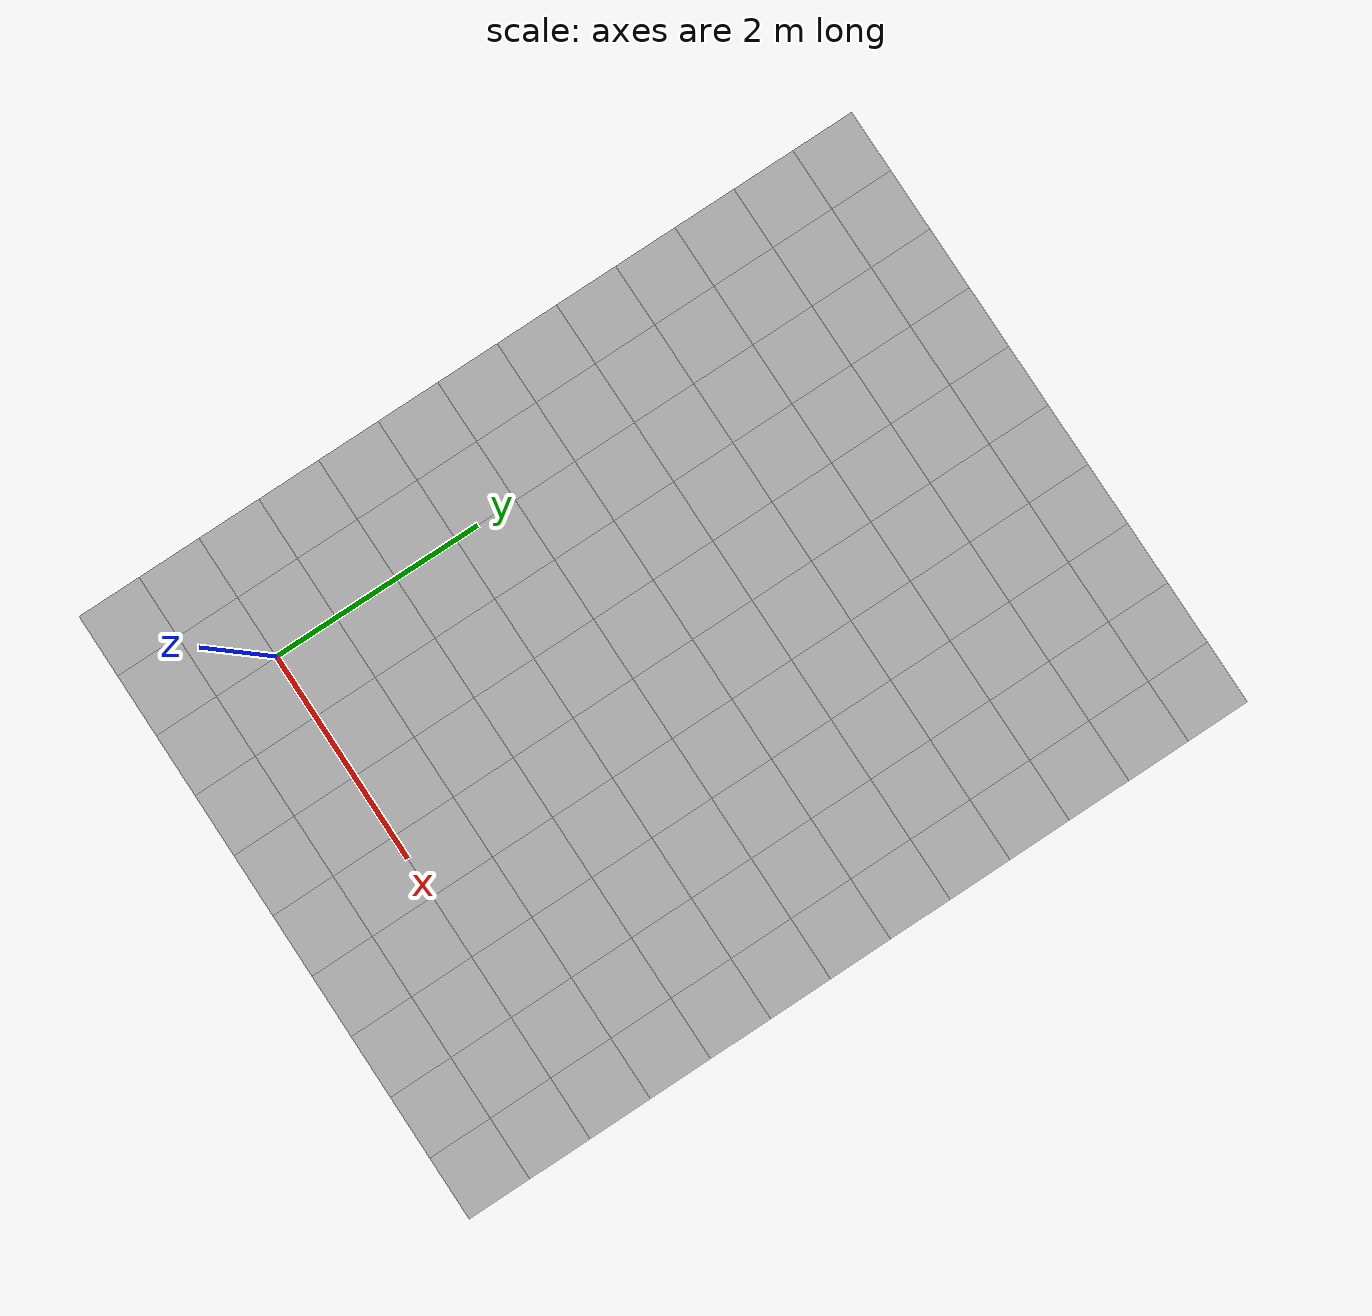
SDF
<sdf version="1.4">
 <world name="default">
  <light name="sun" type="directional">
   <pose>0 0 10 0 -0 0</pose>
   <diffuse>0.8 0.8 0.8 1</diffuse>
   <specular>0.2 0.2 0.2 1</specular>
   <attenuation>
    <range>1000</range>
    <constant>0.9</constant>
    <linear>0.01</linear>
    <quadratic>0.001</quadratic>
   </attenuation>
   <direction>-0.5 0.1 -0.9</direction>
  </light>
  <physics type="ode">
   <max_step_size>0.001</max_step_size>
   <real_time_factor>1</real_time_factor>
   <real_time_update_rate>1000</real_time_update_rate>
   <gravity>0 0 -9.8</gravity>
  </physics>
  <scene><ambient>0.4 0.4 0.4 1</ambient><background>0.7 0.7 0.7 1</background><shadows>1</shadows></scene>
  <spherical_coordinates>
   <surface_model>EARTH_WGS84</surface_model>
   <latitude_deg>0</latitude_deg>
   <longitude_deg>0</longitude_deg>
   <elevation>0</elevation>
   <heading_deg>0</heading_deg>
  </spherical_coordinates>
  <model name="town">
   <link name="tile_-1_-1">
    <pose>-0.595 -0.595 0 0 -0 0</pose>
    <inertial>
     <pose>0.2975 0.2975 -0.005 0 -0 0</pose>
     <mass>100</mass>
     <inertia><ixx>0</ixx><ixy>0</ixy><ixz>0</ixz><iyy>0</iyy><iyz>0</iyz><izz>0</izz></inertia>
    </inertial>
    <collision name="tile_-1_-1_collision">
     <pose>0.2975 0.2975 -0.005 0 -0 0</pose>
     <geometry><box><size>0.595 0.595 0.01</size></box></geometry>
    </collision>
    <visual name="tile_-1_-1_visual">
     <pose>0.2975 0.2975 -0.005 0 -0 0</pose>
     <geometry>
      <mesh>
       <scale>1 1 1</scale>
       <uri>/home/yinann/duckietown/catkin_ws/src/duckietown_description/urdf/meshes/empty.dae</uri>
      </mesh>
     </geometry>
    </visual>
    <velocity_decay><linear>0</linear><angular>0</angular></velocity_decay>
   </link>
   <joint name="world_to_tile_-1_-1" type="revolute">
    <child>tile_-1_-1</child>
    <parent>world</parent>
    <axis>
     <limit><lower>0</lower><upper>0</upper></limit>
     <dynamics><damping>0</damping></dynamics>
     <xyz>0 0 1</xyz>
    </axis>
   </joint>
   <link name="tile_-1_-2">
    <pose>-0.595 -1.19 0 0 -0 0</pose>
    <inertial>
     <pose>0.2975 0.2975 -0.005 0 -0 0</pose>
     <mass>100</mass>
     <inertia><ixx>0</ixx><ixy>0</ixy><ixz>0</ixz><iyy>0</iyy><iyz>0</iyz><izz>0</izz></inertia>
    </inertial>
    <collision name="tile_-1_-2_collision">
     <pose>0.2975 0.2975 -0.005 0 -0 0</pose>
     <geometry><box><size>0.595 0.595 0.01</size></box></geometry>
    </collision>
    <visual name="tile_-1_-2_visual">
     <pose>0.2975 0.2975 -0.005 0 -0 0</pose>
     <geometry>
      <mesh>
       <scale>1 1 1</scale>
       <uri>/home/yinann/duckietown/catkin_ws/src/duckietown_description/urdf/meshes/empty.dae</uri>
      </mesh>
     </geometry>
    </visual>
    <velocity_decay><linear>0</linear><angular>0</angular></velocity_decay>
   </link>
   <joint name="world_to_tile_-1_-2" type="revolute">
    <child>tile_-1_-2</child>
    <parent>world</parent>
    <axis>
     <limit><lower>0</lower><upper>0</upper></limit>
     <dynamics><damping>0</damping></dynamics>
     <xyz>0 0 1</xyz>
    </axis>
   </joint>
   <link name="tile_-1_0">
    <pose>-0.595 0 0 0 -0 0</pose>
    <inertial>
     <pose>0.2975 0.2975 -0.005 0 -0 0</pose>
     <mass>100</mass>
     <inertia><ixx>0</ixx><ixy>0</ixy><ixz>0</ixz><iyy>0</iyy><iyz>0</iyz><izz>0</izz></inertia>
    </inertial>
    <collision name="tile_-1_0_collision">
     <pose>0.2975 0.2975 -0.005 0 -0 0</pose>
     <geometry><box><size>0.595 0.595 0.01</size></box></geometry>
    </collision>
    <visual name="tile_-1_0_visual">
     <pose>0.2975 0.2975 -0.005 0 -0 0</pose>
     <geometry>
      <mesh>
       <scale>1 1 1</scale>
       <uri>/home/yinann/duckietown/catkin_ws/src/duckietown_description/urdf/meshes/empty.dae</uri>
      </mesh>
     </geometry>
    </visual>
    <velocity_decay><linear>0</linear><angular>0</angular></velocity_decay>
   </link>
   <joint name="world_to_tile_-1_0" type="revolute">
    <child>tile_-1_0</child>
    <parent>world</parent>
    <axis>
     <limit><lower>0</lower><upper>0</upper></limit>
     <dynamics><damping>0</damping></dynamics>
     <xyz>0 0 1</xyz>
    </axis>
   </joint>
   <link name="tile_-1_1">
    <pose>-0.595 0.595 0 0 -0 0</pose>
    <inertial>
     <pose>0.2975 0.2975 -0.005 0 -0 0</pose>
     <mass>100</mass>
     <inertia><ixx>0</ixx><ixy>0</ixy><ixz>0</ixz><iyy>0</iyy><iyz>0</iyz><izz>0</izz></inertia>
    </inertial>
    <collision name="tile_-1_1_collision">
     <pose>0.2975 0.2975 -0.005 0 -0 0</pose>
     <geometry><box><size>0.595 0.595 0.01</size></box></geometry>
    </collision>
    <visual name="tile_-1_1_visual">
     <pose>0.2975 0.2975 -0.005 0 -0 0</pose>
     <geometry>
      <mesh>
       <scale>1 1 1</scale>
       <uri>/home/yinann/duckietown/catkin_ws/src/duckietown_description/urdf/meshes/empty.dae</uri>
      </mesh>
     </geometry>
    </visual>
    <velocity_decay><linear>0</linear><angular>0</angular></velocity_decay>
   </link>
   <joint name="world_to_tile_-1_1" type="revolute">
    <child>tile_-1_1</child>
    <parent>world</parent>
    <axis>
     <limit><lower>0</lower><upper>0</upper></limit>
     <dynamics><damping>0</damping></dynamics>
     <xyz>0 0 1</xyz>
    </axis>
   </joint>
   <link name="tile_-1_10">
    <pose>-0.595 5.95 0 0 -0 0</pose>
    <inertial>
     <pose>0.2975 0.2975 -0.005 0 -0 0</pose>
     <mass>100</mass>
     <inertia><ixx>0</ixx><ixy>0</ixy><ixz>0</ixz><iyy>0</iyy><iyz>0</iyz><izz>0</izz></inertia>
    </inertial>
    <collision name="tile_-1_10_collision">
     <pose>0.2975 0.2975 -0.005 0 -0 0</pose>
     <geometry><box><size>0.595 0.595 0.01</size></box></geometry>
    </collision>
    <visual name="tile_-1_10_visual">
     <pose>0.2975 0.2975 -0.005 0 -0 0</pose>
     <geometry>
      <mesh>
       <scale>1 1 1</scale>
       <uri>/home/yinann/duckietown/catkin_ws/src/duckietown_description/urdf/meshes/empty.dae</uri>
      </mesh>
     </geometry>
    </visual>
    <velocity_decay><linear>0</linear><angular>0</angular></velocity_decay>
   </link>
   <joint name="world_to_tile_-1_10" type="revolute">
    <child>tile_-1_10</child>
    <parent>world</parent>
    <axis>
     <limit><lower>0</lower><upper>0</upper></limit>
     <dynamics><damping>0</damping></dynamics>
     <xyz>0 0 1</xyz>
    </axis>
   </joint>
   <link name="tile_-1_2">
    <pose>-0.595 1.19 0 0 -0 0</pose>
    <inertial>
     <pose>0.2975 0.2975 -0.005 0 -0 0</pose>
     <mass>100</mass>
     <inertia><ixx>0</ixx><ixy>0</ixy><ixz>0</ixz><iyy>0</iyy><iyz>0</iyz><izz>0</izz></inertia>
    </inertial>
    <collision name="tile_-1_2_collision">
     <pose>0.2975 0.2975 -0.005 0 -0 0</pose>
     <geometry><box><size>0.595 0.595 0.01</size></box></geometry>
    </collision>
    <visual name="tile_-1_2_visual">
     <pose>0.2975 0.2975 -0.005 0 -0 0</pose>
     <geometry>
      <mesh>
       <scale>1 1 1</scale>
       <uri>/home/yinann/duckietown/catkin_ws/src/duckietown_description/urdf/meshes/empty.dae</uri>
      </mesh>
     </geometry>
    </visual>
    <velocity_decay><linear>0</linear><angular>0</angular></velocity_decay>
   </link>
   <joint name="world_to_tile_-1_2" type="revolute">
    <child>tile_-1_2</child>
    <parent>world</parent>
    <axis>
     <limit><lower>0</lower><upper>0</upper></limit>
     <dynamics><damping>0</damping></dynamics>
     <xyz>0 0 1</xyz>
    </axis>
   </joint>
   <link name="tile_-1_3">
    <pose>-0.595 1.785 0 0 -0 0</pose>
    <inertial>
     <pose>0.2975 0.2975 -0.005 0 -0 0</pose>
     <mass>100</mass>
     <inertia><ixx>0</ixx><ixy>0</ixy><ixz>0</ixz><iyy>0</iyy><iyz>0</iyz><izz>0</izz></inertia>
    </inertial>
    <collision name="tile_-1_3_collision">
     <pose>0.2975 0.2975 -0.005 0 -0 0</pose>
     <geometry><box><size>0.595 0.595 0.01</size></box></geometry>
    </collision>
    <visual name="tile_-1_3_visual">
     <pose>0.2975 0.2975 -0.005 0 -0 0</pose>
     <geometry>
      <mesh>
       <scale>1 1 1</scale>
       <uri>/home/yinann/duckietown/catkin_ws/src/duckietown_description/urdf/meshes/empty.dae</uri>
      </mesh>
     </geometry>
    </visual>
    <velocity_decay><linear>0</linear><angular>0</angular></velocity_decay>
   </link>
   <joint name="world_to_tile_-1_3" type="revolute">
    <child>tile_-1_3</child>
    <parent>world</parent>
    <axis>
     <limit><lower>0</lower><upper>0</upper></limit>
     <dynamics><damping>0</damping></dynamics>
     <xyz>0 0 1</xyz>
    </axis>
   </joint>
   <link name="tile_-1_4">
    <pose>-0.595 2.38 0 0 -0 0</pose>
    <inertial>
     <pose>0.2975 0.2975 -0.005 0 -0 0</pose>
     <mass>100</mass>
     <inertia><ixx>0</ixx><ixy>0</ixy><ixz>0</ixz><iyy>0</iyy><iyz>0</iyz><izz>0</izz></inertia>
    </inertial>
    <collision name="tile_-1_4_collision">
     <pose>0.2975 0.2975 -0.005 0 -0 0</pose>
     <geometry><box><size>0.595 0.595 0.01</size></box></geometry>
    </collision>
    <visual name="tile_-1_4_visual">
     <pose>0.2975 0.2975 -0.005 0 -0 0</pose>
     <geometry>
      <mesh>
       <scale>1 1 1</scale>
       <uri>/home/yinann/duckietown/catkin_ws/src/duckietown_description/urdf/meshes/empty.dae</uri>
      </mesh>
     </geometry>
    </visual>
    <velocity_decay><linear>0</linear><angular>0</angular></velocity_decay>
   </link>
   <joint name="world_to_tile_-1_4" type="revolute">
    <child>tile_-1_4</child>
    <parent>world</parent>
    <axis>
     <limit><lower>0</lower><upper>0</upper></limit>
     <dynamics><damping>0</damping></dynamics>
     <xyz>0 0 1</xyz>
    </axis>
   </joint>
   <link name="tile_-1_5">
    <pose>-0.595 2.975 0 0 -0 0</pose>
    <inertial>
     <pose>0.2975 0.2975 -0.005 0 -0 0</pose>
     <mass>100</mass>
     <inertia><ixx>0</ixx><ixy>0</ixy><ixz>0</ixz><iyy>0</iyy><iyz>0</iyz><izz>0</izz></inertia>
    </inertial>
    <collision name="tile_-1_5_collision">
     <pose>0.2975 0.2975 -0.005 0 -0 0</pose>
     <geometry><box><size>0.595 0.595 0.01</size></box></geometry>
    </collision>
    <visual name="tile_-1_5_visual">
     <pose>0.2975 0.2975 -0.005 0 -0 0</pose>
     <geometry>
      <mesh>
       <scale>1 1 1</scale>
       <uri>/home/yinann/duckietown/catkin_ws/src/duckietown_description/urdf/meshes/empty.dae</uri>
      </mesh>
     </geometry>
    </visual>
    <velocity_decay><linear>0</linear><angular>0</angular></velocity_decay>
   </link>
   <joint name="world_to_tile_-1_5" type="revolute">
    <child>tile_-1_5</child>
    <parent>world</parent>
    <axis>
     <limit><lower>0</lower><upper>0</upper></limit>
     <dynamics><damping>0</damping></dynamics>
     <xyz>0 0 1</xyz>
    </axis>
   </joint>
   <link name="tile_-1_6">
    <pose>-0.595 3.57 0 0 -0 0</pose>
    <inertial>
     <pose>0.2975 0.2975 -0.005 0 -0 0</pose>
     <mass>100</mass>
     <inertia><ixx>0</ixx><ixy>0</ixy><ixz>0</ixz><iyy>0</iyy><iyz>0</iyz><izz>0</izz></inertia>
    </inertial>
    <collision name="tile_-1_6_collision">
     <pose>0.2975 0.2975 -0.005 0 -0 0</pose>
     <geometry><box><size>0.595 0.595 0.01</size></box></geometry>
    </collision>
    <visual name="tile_-1_6_visual">
     <pose>0.2975 0.2975 -0.005 0 -0 0</pose>
     <geometry>
      <mesh>
       <scale>1 1 1</scale>
       <uri>/home/yinann/duckietown/catkin_ws/src/duckietown_description/urdf/meshes/empty.dae</uri>
      </mesh>
     </geometry>
    </visual>
    <velocity_decay><linear>0</linear><angular>0</angular></velocity_decay>
   </link>
   <joint name="world_to_tile_-1_6" type="revolute">
    <child>tile_-1_6</child>
    <parent>world</parent>
    <axis>
     <limit><lower>0</lower><upper>0</upper></limit>
     <dynamics><damping>0</damping></dynamics>
     <xyz>0 0 1</xyz>
    </axis>
   </joint>
   <link name="tile_-1_7">
    <pose>-0.595 4.165 0 0 -0 0</pose>
    <inertial>
     <pose>0.2975 0.2975 -0.005 0 -0 0</pose>
     <mass>100</mass>
     <inertia><ixx>0</ixx><ixy>0</ixy><ixz>0</ixz><iyy>0</iyy><iyz>0</iyz><izz>0</izz></inertia>
    </inertial>
    <collision name="tile_-1_7_collision">
     <pose>0.2975 0.2975 -0.005 0 -0 0</pose>
     <geometry><box><size>0.595 0.595 0.01</size></box></geometry>
    </collision>
    <visual name="tile_-1_7_visual">
     <pose>0.2975 0.2975 -0.005 0 -0 0</pose>
     <geometry>
      <mesh>
       <scale>1 1 1</scale>
       <uri>/home/yinann/duckietown/catkin_ws/src/duckietown_description/urdf/meshes/empty.dae</uri>
      </mesh>
     </geometry>
    </visual>
    <velocity_decay><linear>0</linear><angular>0</angular></velocity_decay>
   </link>
   <joint name="world_to_tile_-1_7" type="revolute">
    <child>tile_-1_7</child>
    <parent>world</parent>
    <axis>
     <limit><lower>0</lower><upper>0</upper></limit>
     <dynamics><damping>0</damping></dynamics>
     <xyz>0 0 1</xyz>
    </axis>
   </joint>
   <link name="tile_-1_8">
    <pose>-0.595 4.76 0 0 -0 0</pose>
    <inertial>
     <pose>0.2975 0.2975 -0.005 0 -0 0</pose>
     <mass>100</mass>
     <inertia><ixx>0</ixx><ixy>0</ixy><ixz>0</ixz><iyy>0</iyy><iyz>0</iyz><izz>0</izz></inertia>
    </inertial>
    <collision name="tile_-1_8_collision">
     <pose>0.2975 0.2975 -0.005 0 -0 0</pose>
     <geometry><box><size>0.595 0.595 0.01</size></box></geometry>
    </collision>
    <visual name="tile_-1_8_visual">
     <pose>0.2975 0.2975 -0.005 0 -0 0</pose>
     <geometry>
      <mesh>
       <scale>1 1 1</scale>
       <uri>/home/yinann/duckietown/catkin_ws/src/duckietown_description/urdf/meshes/empty.dae</uri>
      </mesh>
     </geometry>
    </visual>
    <velocity_decay><linear>0</linear><angular>0</angular></velocity_decay>
   </link>
   <joint name="world_to_tile_-1_8" type="revolute">
    <child>tile_-1_8</child>
    <parent>world</parent>
    <axis>
     <limit><lower>0</lower><upper>0</upper></limit>
     <dynamics><damping>0</damping></dynamics>
     <xyz>0 0 1</xyz>
    </axis>
   </joint>
   <link name="tile_-1_9">
    <pose>-0.595 5.355 0 0 -0 0</pose>
    <inertial>
     <pose>0.2975 0.2975 -0.005 0 -0 0</pose>
     <mass>100</mass>
     <inertia><ixx>0</ixx><ixy>0</ixy><ixz>0</ixz><iyy>0</iyy><iyz>0</iyz><izz>0</izz></inertia>
    </inertial>
    <collision name="tile_-1_9_collision">
     <pose>0.2975 0.2975 -0.005 0 -0 0</pose>
     <geometry><box><size>0.595 0.595 0.01</size></box></geometry>
    </collision>
    <visual name="tile_-1_9_visual">
     <pose>0.2975 0.2975 -0.005 0 -0 0</pose>
     <geometry>
      <mesh>
       <scale>1 1 1</scale>
       <uri>/home/yinann/duckietown/catkin_ws/src/duckietown_description/urdf/meshes/empty.dae</uri>
      </mesh>
     </geometry>
    </visual>
    <velocity_decay><linear>0</linear><angular>0</angular></velocity_decay>
   </link>
   <joint name="world_to_tile_-1_9" type="revolute">
    <child>tile_-1_9</child>
    <parent>world</parent>
    <axis>
     <limit><lower>0</lower><upper>0</upper></limit>
     <dynamics><damping>0</damping></dynamics>
     <xyz>0 0 1</xyz>
    </axis>
   </joint>
   <link name="tile_-2_-1">
    <pose>-1.19 -0.595 0 0 -0 0</pose>
    <inertial>
     <pose>0.2975 0.2975 -0.005 0 -0 0</pose>
     <mass>100</mass>
     <inertia><ixx>0</ixx><ixy>0</ixy><ixz>0</ixz><iyy>0</iyy><iyz>0</iyz><izz>0</izz></inertia>
    </inertial>
    <collision name="tile_-2_-1_collision">
     <pose>0.2975 0.2975 -0.005 0 -0 0</pose>
     <geometry><box><size>0.595 0.595 0.01</size></box></geometry>
    </collision>
    <visual name="tile_-2_-1_visual">
     <pose>0.2975 0.2975 -0.005 0 -0 0</pose>
     <geometry>
      <mesh>
       <scale>1 1 1</scale>
       <uri>/home/yinann/duckietown/catkin_ws/src/duckietown_description/urdf/meshes/empty.dae</uri>
      </mesh>
     </geometry>
    </visual>
    <velocity_decay><linear>0</linear><angular>0</angular></velocity_decay>
   </link>
   <joint name="world_to_tile_-2_-1" type="revolute">
    <child>tile_-2_-1</child>
    <parent>world</parent>
    <axis>
     <limit><lower>0</lower><upper>0</upper></limit>
     <dynamics><damping>0</damping></dynamics>
     <xyz>0 0 1</xyz>
    </axis>
   </joint>
   <link name="tile_-2_-2">
    <pose>-1.19 -1.19 0 0 -0 0</pose>
    <inertial>
     <pose>0.2975 0.2975 -0.005 0 -0 0</pose>
     <mass>100</mass>
     <inertia><ixx>0</ixx><ixy>0</ixy><ixz>0</ixz><iyy>0</iyy><iyz>0</iyz><izz>0</izz></inertia>
    </inertial>
    <collision name="tile_-2_-2_collision">
     <pose>0.2975 0.2975 -0.005 0 -0 0</pose>
     <geometry><box><size>0.595 0.595 0.01</size></box></geometry>
    </collision>
    <visual name="tile_-2_-2_visual">
     <pose>0.2975 0.2975 -0.005 0 -0 0</pose>
     <geometry>
      <mesh>
       <scale>1 1 1</scale>
       <uri>/home/yinann/duckietown/catkin_ws/src/duckietown_description/urdf/meshes/empty.dae</uri>
      </mesh>
     </geometry>
    </visual>
    <velocity_decay><linear>0</linear><angular>0</angular></velocity_decay>
   </link>
   <joint name="world_to_tile_-2_-2" type="revolute">
    <child>tile_-2_-2</child>
    <parent>world</parent>
    <axis>
     <limit><lower>0</lower><upper>0</upper></limit>
     <dynamics><damping>0</damping></dynamics>
     <xyz>0 0 1</xyz>
    </axis>
   </joint>
   <link name="tile_-2_0">
    <pose>-1.19 0 0 0 -0 0</pose>
    <inertial>
     <pose>0.2975 0.2975 -0.005 0 -0 0</pose>
     <mass>100</mass>
     <inertia><ixx>0</ixx><ixy>0</ixy><ixz>0</ixz><iyy>0</iyy><iyz>0</iyz><izz>0</izz></inertia>
    </inertial>
    <collision name="tile_-2_0_collision">
     <pose>0.2975 0.2975 -0.005 0 -0 0</pose>
     <geometry><box><size>0.595 0.595 0.01</size></box></geometry>
    </collision>
    <visual name="tile_-2_0_visual">
     <pose>0.2975 0.2975 -0.005 0 -0 0</pose>
     <geometry>
      <mesh>
       <scale>1 1 1</scale>
       <uri>/home/yinann/duckietown/catkin_ws/src/duckietown_description/urdf/meshes/empty.dae</uri>
      </mesh>
     </geometry>
    </visual>
    <velocity_decay><linear>0</linear><angular>0</angular></velocity_decay>
   </link>
   <joint name="world_to_tile_-2_0" type="revolute">
    <child>tile_-2_0</child>
    <parent>world</parent>
    <axis>
     <limit><lower>0</lower><upper>0</upper></limit>
     <dynamics><damping>0</damping></dynamics>
     <xyz>0 0 1</xyz>
    </axis>
   </joint>
   <link name="tile_-2_1">
    <pose>-1.19 0.595 0 0 -0 0</pose>
    <inertial>
     <pose>0.2975 0.2975 -0.005 0 -0 0</pose>
     <mass>100</mass>
     <inertia><ixx>0</ixx><ixy>0</ixy><ixz>0</ixz><iyy>0</iyy><iyz>0</iyz><izz>0</izz></inertia>
    </inertial>
    <collision name="tile_-2_1_collision">
     <pose>0.2975 0.2975 -0.005 0 -0 0</pose>
     <geometry><box><size>0.595 0.595 0.01</size></box></geometry>
    </collision>
    <visual name="tile_-2_1_visual">
     <pose>0.2975 0.2975 -0.005 0 -0 0</pose>
     <geometry>
      <mesh>
       <scale>1 1 1</scale>
       <uri>/home/yinann/duckietown/catkin_ws/src/duckietown_description/urdf/meshes/empty.dae</uri>
      </mesh>
     </geometry>
    </visual>
    <velocity_decay><linear>0</linear><angular>0</angular></velocity_decay>
   </link>
   <joint name="world_to_tile_-2_1" type="revolute">
    <child>tile_-2_1</child>
    <parent>world</parent>
    <axis>
     <limit><lower>0</lower><upper>0</upper></limit>
     <dynamics><damping>0</damping></dynamics>
     <xyz>0 0 1</xyz>
    </axis>
   </joint>
   <link name="tile_-2_10">
    <pose>-1.19 5.95 0 0 -0 0</pose>
    <inertial>
     <pose>0.2975 0.2975 -0.005 0 -0 0</pose>
     <mass>100</mass>
     <inertia><ixx>0</ixx><ixy>0</ixy><ixz>0</ixz><iyy>0</iyy><iyz>0</iyz><izz>0</izz></inertia>
    </inertial>
    <collision name="tile_-2_10_collision">
     <pose>0.2975 0.2975 -0.005 0 -0 0</pose>
     <geometry><box><size>0.595 0.595 0.01</size></box></geometry>
    </collision>
    <visual name="tile_-2_10_visual">
     <pose>0.2975 0.2975 -0.005 0 -0 0</pose>
     <geometry>
      <mesh>
       <scale>1 1 1</scale>
       <uri>/home/yinann/duckietown/catkin_ws/src/duckietown_description/urdf/meshes/empty.dae</uri>
      </mesh>
     </geometry>
    </visual>
    <velocity_decay><linear>0</linear><angular>0</angular></velocity_decay>
   </link>
   <joint name="world_to_tile_-2_10" type="revolute">
    <child>tile_-2_10</child>
    <parent>world</parent>
    <axis>
     <limit><lower>0</lower><upper>0</upper></limit>
     <dynamics><damping>0</damping></dynamics>
     <xyz>0 0 1</xyz>
    </axis>
   </joint>
   <link name="tile_-2_2">
    <pose>-1.19 1.19 0 0 -0 0</pose>
    <inertial>
     <pose>0.2975 0.2975 -0.005 0 -0 0</pose>
     <mass>100</mass>
     <inertia><ixx>0</ixx><ixy>0</ixy><ixz>0</ixz><iyy>0</iyy><iyz>0</iyz><izz>0</izz></inertia>
    </inertial>
    <collision name="tile_-2_2_collision">
     <pose>0.2975 0.2975 -0.005 0 -0 0</pose>
     <geometry><box><size>0.595 0.595 0.01</size></box></geometry>
    </collision>
    <visual name="tile_-2_2_visual">
     <pose>0.2975 0.2975 -0.005 0 -0 0</pose>
     <geometry>
      <mesh>
       <scale>1 1 1</scale>
       <uri>/home/yinann/duckietown/catkin_ws/src/duckietown_description/urdf/meshes/empty.dae</uri>
      </mesh>
     </geometry>
    </visual>
    <velocity_decay><linear>0</linear><angular>0</angular></velocity_decay>
   </link>
   <joint name="world_to_tile_-2_2" type="revolute">
    <child>tile_-2_2</child>
    <parent>world</parent>
    <axis>
     <limit><lower>0</lower><upper>0</upper></limit>
     <dynamics><damping>0</damping></dynamics>
     <xyz>0 0 1</xyz>
    </axis>
   </joint>
   <link name="tile_-2_3">
    <pose>-1.19 1.785 0 0 -0 0</pose>
    <inertial>
     <pose>0.2975 0.2975 -0.005 0 -0 0</pose>
     <mass>100</mass>
     <inertia><ixx>0</ixx><ixy>0</ixy><ixz>0</ixz><iyy>0</iyy><iyz>0</iyz><izz>0</izz></inertia>
    </inertial>
    <collision name="tile_-2_3_collision">
     <pose>0.2975 0.2975 -0.005 0 -0 0</pose>
     <geometry><box><size>0.595 0.595 0.01</size></box></geometry>
    </collision>
    <visual name="tile_-2_3_visual">
     <pose>0.2975 0.2975 -0.005 0 -0 0</pose>
     <geometry>
      <mesh>
       <scale>1 1 1</scale>
       <uri>/home/yinann/duckietown/catkin_ws/src/duckietown_description/urdf/meshes/empty.dae</uri>
      </mesh>
     </geometry>
    </visual>
    <velocity_decay><linear>0</linear><angular>0</angular></velocity_decay>
   </link>
   <joint name="world_to_tile_-2_3" type="revolute">
    <child>tile_-2_3</child>
    <parent>world</parent>
    <axis>
     <limit><lower>0</lower><upper>0</upper></limit>
     <dynamics><damping>0</damping></dynamics>
     <xyz>0 0 1</xyz>
    </axis>
   </joint>
   <link name="tile_-2_4">
    <pose>-1.19 2.38 0 0 -0 0</pose>
    <inertial>
     <pose>0.2975 0.2975 -0.005 0 -0 0</pose>
     <mass>100</mass>
     <inertia><ixx>0</ixx><ixy>0</ixy><ixz>0</ixz><iyy>0</iyy><iyz>0</iyz><izz>0</izz></inertia>
    </inertial>
    <collision name="tile_-2_4_collision">
     <pose>0.2975 0.2975 -0.005 0 -0 0</pose>
     <geometry><box><size>0.595 0.595 0.01</size></box></geometry>
    </collision>
    <visual name="tile_-2_4_visual">
     <pose>0.2975 0.2975 -0.005 0 -0 0</pose>
     <geometry>
      <mesh>
       <scale>1 1 1</scale>
       <uri>/home/yinann/duckietown/catkin_ws/src/duckietown_description/urdf/meshes/empty.dae</uri>
      </mesh>
     </geometry>
    </visual>
    <velocity_decay><linear>0</linear><angular>0</angular></velocity_decay>
   </link>
   <joint name="world_to_tile_-2_4" type="revolute">
    <child>tile_-2_4</child>
    <parent>world</parent>
    <axis>
     <limit><lower>0</lower><upper>0</upper></limit>
     <dynamics><damping>0</damping></dynamics>
     <xyz>0 0 1</xyz>
    </axis>
   </joint>
   <link name="tile_-2_5">
    <pose>-1.19 2.975 0 0 -0 0</pose>
    <inertial>
     <pose>0.2975 0.2975 -0.005 0 -0 0</pose>
     <mass>100</mass>
     <inertia><ixx>0</ixx><ixy>0</ixy><ixz>0</ixz><iyy>0</iyy><iyz>0</iyz><izz>0</izz></inertia>
    </inertial>
    <collision name="tile_-2_5_collision">
     <pose>0.2975 0.2975 -0.005 0 -0 0</pose>
     <geometry><box><size>0.595 0.595 0.01</size></box></geometry>
    </collision>
    <visual name="tile_-2_5_visual">
     <pose>0.2975 0.2975 -0.005 0 -0 0</pose>
     <geometry>
      <mesh>
       <scale>1 1 1</scale>
       <uri>/home/yinann/duckietown/catkin_ws/src/duckietown_description/urdf/meshes/empty.dae</uri>
      </mesh>
     </geometry>
    </visual>
    <velocity_decay><linear>0</linear><angular>0</angular></velocity_decay>
   </link>
   <joint name="world_to_tile_-2_5" type="revolute">
    <child>tile_-2_5</child>
    <parent>world</parent>
    <axis>
     <limit><lower>0</lower><upper>0</upper></limit>
     <dynamics><damping>0</damping></dynamics>
     <xyz>0 0 1</xyz>
    </axis>
   </joint>
   <link name="tile_-2_6">
    <pose>-1.19 3.57 0 0 -0 0</pose>
    <inertial>
     <pose>0.2975 0.2975 -0.005 0 -0 0</pose>
     <mass>100</mass>
     <inertia><ixx>0</ixx><ixy>0</ixy><ixz>0</ixz><iyy>0</iyy><iyz>0</iyz><izz>0</izz></inertia>
    </inertial>
    <collision name="tile_-2_6_collision">
     <pose>0.2975 0.2975 -0.005 0 -0 0</pose>
     <geometry><box><size>0.595 0.595 0.01</size></box></geometry>
    </collision>
    <visual name="tile_-2_6_visual">
     <pose>0.2975 0.2975 -0.005 0 -0 0</pose>
     <geometry>
      <mesh>
       <scale>1 1 1</scale>
       <uri>/home/yinann/duckietown/catkin_ws/src/duckietown_description/urdf/meshes/empty.dae</uri>
      </mesh>
     </geometry>
    </visual>
    <velocity_decay><linear>0</linear><angular>0</angular></velocity_decay>
   </link>
   <joint name="world_to_tile_-2_6" type="revolute">
    <child>tile_-2_6</child>
    <parent>world</parent>
    <axis>
     <limit><lower>0</lower><upper>0</upper></limit>
     <dynamics><damping>0</damping></dynamics>
     <xyz>0 0 1</xyz>
    </axis>
   </joint>
   <link name="tile_-2_7">
    <pose>-1.19 4.165 0 0 -0 0</pose>
    <inertial>
     <pose>0.2975 0.2975 -0.005 0 -0 0</pose>
     <mass>100</mass>
     <inertia><ixx>0</ixx><ixy>0</ixy><ixz>0</ixz><iyy>0</iyy><iyz>0</iyz><izz>0</izz></inertia>
    </inertial>
    <collision name="tile_-2_7_collision">
     <pose>0.2975 0.2975 -0.005 0 -0 0</pose>
     <geometry><box><size>0.595 0.595 0.01</size></box></geometry>
    </collision>
    <visual name="tile_-2_7_visual">
     <pose>0.2975 0.2975 -0.005 0 -0 0</pose>
     <geometry>
      <mesh>
       <scale>1 1 1</scale>
       <uri>/home/yinann/duckietown/catkin_ws/src/duckietown_description/urdf/meshes/empty.dae</uri>
      </mesh>
     </geometry>
    </visual>
    <velocity_decay><linear>0</linear><angular>0</angular></velocity_decay>
   </link>
   <joint name="world_to_tile_-2_7" type="revolute">
    <child>tile_-2_7</child>
    <parent>world</parent>
    <axis>
     <limit><lower>0</lower><upper>0</upper></limit>
     <dynamics><damping>0</damping></dynamics>
     <xyz>0 0 1</xyz>
    </axis>
   </joint>
   <link name="tile_-2_8">
    <pose>-1.19 4.76 0 0 -0 0</pose>
    <inertial>
     <pose>0.2975 0.2975 -0.005 0 -0 0</pose>
     <mass>100</mass>
     <inertia><ixx>0</ixx><ixy>0</ixy><ixz>0</ixz><iyy>0</iyy><iyz>0</iyz><izz>0</izz></inertia>
    </inertial>
    <collision name="tile_-2_8_collision">
     <pose>0.2975 0.2975 -0.005 0 -0 0</pose>
     <geometry><box><size>0.595 0.595 0.01</size></box></geometry>
    </collision>
    <visual name="tile_-2_8_visual">
     <pose>0.2975 0.2975 -0.005 0 -0 0</pose>
     <geometry>
      <mesh>
       <scale>1 1 1</scale>
       <uri>/home/yinann/duckietown/catkin_ws/src/duckietown_description/urdf/meshes/empty.dae</uri>
      </mesh>
     </geometry>
    </visual>
    <velocity_decay><linear>0</linear><angular>0</angular></velocity_decay>
   </link>
   <joint name="world_to_tile_-2_8" type="revolute">
    <child>tile_-2_8</child>
    <parent>world</parent>
    <axis>
     <limit><lower>0</lower><upper>0</upper></limit>
     <dynamics><damping>0</damping></dynamics>
     <xyz>0 0 1</xyz>
    </axis>
   </joint>
   <link name="tile_-2_9">
    <pose>-1.19 5.355 0 0 -0 0</pose>
    <inertial>
     <pose>0.2975 0.2975 -0.005 0 -0 0</pose>
     <mass>100</mass>
     <inertia><ixx>0</ixx><ixy>0</ixy><ixz>0</ixz><iyy>0</iyy><iyz>0</iyz><izz>0</izz></inertia>
    </inertial>
    <collision name="tile_-2_9_collision">
     <pose>0.2975 0.2975 -0.005 0 -0 0</pose>
     <geometry><box><size>0.595 0.595 0.01</size></box></geometry>
    </collision>
    <visual name="tile_-2_9_visual">
     <pose>0.2975 0.2975 -0.005 0 -0 0</pose>
     <geometry>
      <mesh>
       <scale>1 1 1</scale>
       <uri>/home/yinann/duckietown/catkin_ws/src/duckietown_description/urdf/meshes/empty.dae</uri>
      </mesh>
     </geometry>
    </visual>
    <velocity_decay><linear>0</linear><angular>0</angular></velocity_decay>
   </link>
   <joint name="world_to_tile_-2_9" type="revolute">
    <child>tile_-2_9</child>
    <parent>world</parent>
    <axis>
     <limit><lower>0</lower><upper>0</upper></limit>
     <dynamics><damping>0</damping></dynamics>
     <xyz>0 0 1</xyz>
    </axis>
   </joint>
   <link name="tile_0_-1">
    <pose>0 -0.595 0 0 -0 0</pose>
    <inertial>
     <pose>0.2975 0.2975 -0.005 0 -0 0</pose>
     <mass>100</mass>
     <inertia><ixx>0</ixx><ixy>0</ixy><ixz>0</ixz><iyy>0</iyy><iyz>0</iyz><izz>0</izz></inertia>
    </inertial>
    <collision name="tile_0_-1_collision">
     <pose>0.2975 0.2975 -0.005 0 -0 0</pose>
     <geometry><box><size>0.595 0.595 0.01</size></box></geometry>
    </collision>
    <visual name="tile_0_-1_visual">
     <pose>0.2975 0.2975 -0.005 0 -0 0</pose>
     <geometry>
      <mesh>
       <scale>1 1 1</scale>
       <uri>/home/yinann/duckietown/catkin_ws/src/duckietown_description/urdf/meshes/empty.dae</uri>
      </mesh>
     </geometry>
    </visual>
    <velocity_decay><linear>0</linear><angular>0</angular></velocity_decay>
   </link>
   <joint name="world_to_tile_0_-1" type="revolute">
    <child>tile_0_-1</child>
    <parent>world</parent>
    <axis>
     <limit><lower>0</lower><upper>0</upper></limit>
     <dynamics><damping>0</damping></dynamics>
     <xyz>0 0 1</xyz>
    </axis>
   </joint>
   <link name="tile_0_-2">
    <pose>0 -1.19 0 0 -0 0</pose>
    <inertial>
     <pose>0.2975 0.2975 -0.005 0 -0 0</pose>
     <mass>100</mass>
     <inertia><ixx>0</ixx><ixy>0</ixy><ixz>0</ixz><iyy>0</iyy><iyz>0</iyz><izz>0</izz></inertia>
    </inertial>
    <collision name="tile_0_-2_collision">
     <pose>0.2975 0.2975 -0.005 0 -0 0</pose>
     <geometry><box><size>0.595 0.595 0.01</size></box></geometry>
    </collision>
    <visual name="tile_0_-2_visual">
     <pose>0.2975 0.2975 -0.005 0 -0 0</pose>
     <geometry>
      <mesh>
       <scale>1 1 1</scale>
       <uri>/home/yinann/duckietown/catkin_ws/src/duckietown_description/urdf/meshes/empty.dae</uri>
      </mesh>
     </geometry>
    </visual>
    <velocity_decay><linear>0</linear><angular>0</angular></velocity_decay>
   </link>
   <joint name="world_to_tile_0_-2" type="revolute">
    <child>tile_0_-2</child>
    <parent>world</parent>
    <axis>
     <limit><lower>0</lower><upper>0</upper></limit>
     <dynamics><damping>0</damping></dynamics>
     <xyz>0 0 1</xyz>
    </axis>
   </joint>
   <link name="tile_0_0">
    <inertial>
     <pose>0.2975 0.2975 -0.005 0 -0 0</pose>
     <mass>100</mass>
     <inertia><ixx>0</ixx><ixy>0</ixy><ixz>0</ixz><iyy>0</iyy><iyz>0</iyz><izz>0</izz></inertia>
    </inertial>
    <collision name="tile_0_0_collision">
     <pose>0.2975 0.2975 -0.005 0 -0 0</pose>
     <geometry><box><size>0.595 0.595 0.01</size></box></geometry>
    </collision>
    <visual name="tile_0_0_visual">
     <pose>0.2975 0.2975 -0.005 0 -0 -1.5708</pose>
     <geometry>
      <mesh>
       <scale>1 1 1</scale>
       <uri>/home/yinann/duckietown/catkin_ws/src/duckietown_description/urdf/meshes/turn.dae</uri>
      </mesh>
     </geometry>
    </visual>
    <velocity_decay><linear>0</linear><angular>0</angular></velocity_decay>
   </link>
   <joint name="world_to_tile_0_0" type="revolute">
    <child>tile_0_0</child>
    <parent>world</parent>
    <axis>
     <limit><lower>0</lower><upper>0</upper></limit>
     <dynamics><damping>0</damping></dynamics>
     <xyz>0 0 1</xyz>
    </axis>
   </joint>
   <link name="tile_0_1">
    <pose>0 0.595 0 0 -0 0</pose>
    <inertial>
     <pose>0.2975 0.2975 -0.005 0 -0 0</pose>
     <mass>100</mass>
     <inertia><ixx>0</ixx><ixy>0</ixy><ixz>0</ixz><iyy>0</iyy><iyz>0</iyz><izz>0</izz></inertia>
    </inertial>
    <collision name="tile_0_1_collision">
     <pose>0.2975 0.2975 -0.005 0 -0 0</pose>
     <geometry><box><size>0.595 0.595 0.01</size></box></geometry>
    </collision>
    <visual name="tile_0_1_visual">
     <pose>0.2975 0.2975 -0.005 0 -0 1.5708</pose>
     <geometry>
      <mesh>
       <scale>1 1 1</scale>
       <uri>/home/yinann/duckietown/catkin_ws/src/duckietown_description/urdf/meshes/straight.dae</uri>
      </mesh>
     </geometry>
    </visual>
    <velocity_decay><linear>0</linear><angular>0</angular></velocity_decay>
   </link>
   <joint name="world_to_tile_0_1" type="revolute">
    <child>tile_0_1</child>
    <parent>world</parent>
    <axis>
     <limit><lower>0</lower><upper>0</upper></limit>
     <dynamics><damping>0</damping></dynamics>
     <xyz>0 0 1</xyz>
    </axis>
   </joint>
   <link name="tile_0_10">
    <pose>0 5.95 0 0 -0 0</pose>
    <inertial>
     <pose>0.2975 0.2975 -0.005 0 -0 0</pose>
     <mass>100</mass>
     <inertia><ixx>0</ixx><ixy>0</ixy><ixz>0</ixz><iyy>0</iyy><iyz>0</iyz><izz>0</izz></inertia>
    </inertial>
    <collision name="tile_0_10_collision">
     <pose>0.2975 0.2975 -0.005 0 -0 0</pose>
     <geometry><box><size>0.595 0.595 0.01</size></box></geometry>
    </collision>
    <visual name="tile_0_10_visual">
     <pose>0.2975 0.2975 -0.005 0 -0 0</pose>
     <geometry>
      <mesh>
       <scale>1 1 1</scale>
       <uri>/home/yinann/duckietown/catkin_ws/src/duckietown_description/urdf/meshes/empty.dae</uri>
      </mesh>
     </geometry>
    </visual>
    <velocity_decay><linear>0</linear><angular>0</angular></velocity_decay>
   </link>
   <joint name="world_to_tile_0_10" type="revolute">
    <child>tile_0_10</child>
    <parent>world</parent>
    <axis>
     <limit><lower>0</lower><upper>0</upper></limit>
     <dynamics><damping>0</damping></dynamics>
     <xyz>0 0 1</xyz>
    </axis>
   </joint>
   <link name="tile_0_2">
    <pose>0 1.19 0 0 -0 0</pose>
    <inertial>
     <pose>0.2975 0.2975 -0.005 0 -0 0</pose>
     <mass>100</mass>
     <inertia><ixx>0</ixx><ixy>0</ixy><ixz>0</ixz><iyy>0</iyy><iyz>0</iyz><izz>0</izz></inertia>
    </inertial>
    <collision name="tile_0_2_collision">
     <pose>0.2975 0.2975 -0.005 0 -0 0</pose>
     <geometry><box><size>0.595 0.595 0.01</size></box></geometry>
    </collision>
    <visual name="tile_0_2_visual">
     <pose>0.2975 0.2975 -0.005 0 -0 1.5708</pose>
     <geometry>
      <mesh>
       <scale>1 1 1</scale>
       <uri>/home/yinann/duckietown/catkin_ws/src/duckietown_description/urdf/meshes/straight.dae</uri>
      </mesh>
     </geometry>
    </visual>
    <velocity_decay><linear>0</linear><angular>0</angular></velocity_decay>
   </link>
   <joint name="world_to_tile_0_2" type="revolute">
    <child>tile_0_2</child>
    <parent>world</parent>
    <axis>
     <limit><lower>0</lower><upper>0</upper></limit>
     <dynamics><damping>0</damping></dynamics>
     <xyz>0 0 1</xyz>
    </axis>
   </joint>
   <link name="tile_0_3">
    <pose>0 1.785 0 0 -0 0</pose>
    <inertial>
     <pose>0.2975 0.2975 -0.005 0 -0 0</pose>
     <mass>100</mass>
     <inertia><ixx>0</ixx><ixy>0</ixy><ixz>0</ixz><iyy>0</iyy><iyz>0</iyz><izz>0</izz></inertia>
    </inertial>
    <collision name="tile_0_3_collision">
     <pose>0.2975 0.2975 -0.005 0 -0 0</pose>
     <geometry><box><size>0.595 0.595 0.01</size></box></geometry>
    </collision>
    <visual name="tile_0_3_visual">
     <pose>0.2975 0.2975 -0.005 0 -0 1.5708</pose>
     <geometry>
      <mesh>
       <scale>1 1 1</scale>
       <uri>/home/yinann/duckietown/catkin_ws/src/duckietown_description/urdf/meshes/straight.dae</uri>
      </mesh>
     </geometry>
    </visual>
    <velocity_decay><linear>0</linear><angular>0</angular></velocity_decay>
   </link>
   <joint name="world_to_tile_0_3" type="revolute">
    <child>tile_0_3</child>
    <parent>world</parent>
    <axis>
     <limit><lower>0</lower><upper>0</upper></limit>
     <dynamics><damping>0</damping></dynamics>
     <xyz>0 0 1</xyz>
    </axis>
   </joint>
   <link name="tile_0_4">
    <pose>0 2.38 0 0 -0 0</pose>
    <inertial>
     <pose>0.2975 0.2975 -0.005 0 -0 0</pose>
     <mass>100</mass>
     <inertia><ixx>0</ixx><ixy>0</ixy><ixz>0</ixz><iyy>0</iyy><iyz>0</iyz><izz>0</izz></inertia>
    </inertial>
    <collision name="tile_0_4_collision">
     <pose>0.2975 0.2975 -0.005 0 -0 0</pose>
     <geometry><box><size>0.595 0.595 0.01</size></box></geometry>
    </collision>
    <visual name="tile_0_4_visual">
     <pose>0.2975 0.2975 -0.005 0 -0 1.5708</pose>
     <geometry>
      <mesh>
       <scale>1 1 1</scale>
       <uri>/home/yinann/duckietown/catkin_ws/src/duckietown_description/urdf/meshes/straight.dae</uri>
      </mesh>
     </geometry>
    </visual>
    <velocity_decay><linear>0</linear><angular>0</angular></velocity_decay>
   </link>
   <joint name="world_to_tile_0_4" type="revolute">
    <child>tile_0_4</child>
    <parent>world</parent>
    <axis>
     <limit><lower>0</lower><upper>0</upper></limit>
     <dynamics><damping>0</damping></dynamics>
     <xyz>0 0 1</xyz>
    </axis>
   </joint>
   <link name="tile_0_5">
    <pose>0 2.975 0 0 -0 0</pose>
    <inertial>
     <pose>0.2975 0.2975 -0.005 0 -0 0</pose>
     <mass>100</mass>
     <inertia><ixx>0</ixx><ixy>0</ixy><ixz>0</ixz><iyy>0</iyy><iyz>0</iyz><izz>0</izz></inertia>
    </inertial>
    <collision name="tile_0_5_collision">
     <pose>0.2975 0.2975 -0.005 0 -0 0</pose>
     <geometry><box><size>0.595 0.595 0.01</size></box></geometry>
    </collision>
    <visual name="tile_0_5_visual">
     <pose>0.2975 0.2975 -0.005 0 -0 1.5708</pose>
     <geometry>
      <mesh>
       <scale>1 1 1</scale>
       <uri>/home/yinann/duckietown/catkin_ws/src/duckietown_description/urdf/meshes/straight.dae</uri>
      </mesh>
     </geometry>
    </visual>
    <velocity_decay><linear>0</linear><angular>0</angular></velocity_decay>
   </link>
   <joint name="world_to_tile_0_5" type="revolute">
    <child>tile_0_5</child>
    <parent>world</parent>
    <axis>
     <limit><lower>0</lower><upper>0</upper></limit>
     <dynamics><damping>0</damping></dynamics>
     <xyz>0 0 1</xyz>
    </axis>
   </joint>
   <link name="tile_0_6">
    <pose>0 3.57 0 0 -0 0</pose>
    <inertial>
     <pose>0.2975 0.2975 -0.005 0 -0 0</pose>
     <mass>100</mass>
     <inertia><ixx>0</ixx><ixy>0</ixy><ixz>0</ixz><iyy>0</iyy><iyz>0</iyz><izz>0</izz></inertia>
    </inertial>
    <collision name="tile_0_6_collision">
     <pose>0.2975 0.2975 -0.005 0 -0 0</pose>
     <geometry><box><size>0.595 0.595 0.01</size></box></geometry>
    </collision>
    <visual name="tile_0_6_visual">
     <pose>0.2975 0.2975 -0.005 0 -0 1.5708</pose>
     <geometry>
      <mesh>
       <scale>1 1 1</scale>
       <uri>/home/yinann/duckietown/catkin_ws/src/duckietown_description/urdf/meshes/straight.dae</uri>
      </mesh>
     </geometry>
    </visual>
    <velocity_decay><linear>0</linear><angular>0</angular></velocity_decay>
   </link>
   <joint name="world_to_tile_0_6" type="revolute">
    <child>tile_0_6</child>
    <parent>world</parent>
    <axis>
     <limit><lower>0</lower><upper>0</upper></limit>
     <dynamics><damping>0</damping></dynamics>
     <xyz>0 0 1</xyz>
    </axis>
   </joint>
   <link name="tile_0_7">
    <pose>0 4.165 0 0 -0 0</pose>
    <inertial>
     <pose>0.2975 0.2975 -0.005 0 -0 0</pose>
     <mass>100</mass>
     <inertia><ixx>0</ixx><ixy>0</ixy><ixz>0</ixz><iyy>0</iyy><iyz>0</iyz><izz>0</izz></inertia>
    </inertial>
    <collision name="tile_0_7_collision">
     <pose>0.2975 0.2975 -0.005 0 -0 0</pose>
     <geometry><box><size>0.595 0.595 0.01</size></box></geometry>
    </collision>
    <visual name="tile_0_7_visual">
     <pose>0.2975 0.2975 -0.005 0 -0 1.5708</pose>
     <geometry>
      <mesh>
       <scale>1 1 1</scale>
       <uri>/home/yinann/duckietown/catkin_ws/src/duckietown_description/urdf/meshes/straight.dae</uri>
      </mesh>
     </geometry>
    </visual>
    <velocity_decay><linear>0</linear><angular>0</angular></velocity_decay>
   </link>
   <joint name="world_to_tile_0_7" type="revolute">
    <child>tile_0_7</child>
    <parent>world</parent>
    <axis>
     <limit><lower>0</lower><upper>0</upper></limit>
     <dynamics><damping>0</damping></dynamics>
     <xyz>0 0 1</xyz>
    </axis>
   </joint>
   <link name="tile_0_8">
    <pose>0 4.76 0 0 -0 0</pose>
    <inertial>
     <pose>0.2975 0.2975 -0.005 0 -0 0</pose>
     <mass>100</mass>
     <inertia><ixx>0</ixx><ixy>0</ixy><ixz>0</ixz><iyy>0</iyy><iyz>0</iyz><izz>0</izz></inertia>
    </inertial>
    <collision name="tile_0_8_collision">
     <pose>0.2975 0.2975 -0.005 0 -0 0</pose>
     <geometry><box><size>0.595 0.595 0.01</size></box></geometry>
    </collision>
    <visual name="tile_0_8_visual">
     <pose>0.2975 0.2975 -0.005 0 -0 -3.14159</pose>
     <geometry>
      <mesh>
       <scale>1 1 1</scale>
       <uri>/home/yinann/duckietown/catkin_ws/src/duckietown_description/urdf/meshes/turn.dae</uri>
      </mesh>
     </geometry>
    </visual>
    <velocity_decay><linear>0</linear><angular>0</angular></velocity_decay>
   </link>
   <joint name="world_to_tile_0_8" type="revolute">
    <child>tile_0_8</child>
    <parent>world</parent>
    <axis>
     <limit><lower>0</lower><upper>0</upper></limit>
     <dynamics><damping>0</damping></dynamics>
     <xyz>0 0 1</xyz>
    </axis>
   </joint>
   <link name="tile_0_9">
    <pose>0 5.355 0 0 -0 0</pose>
    <inertial>
     <pose>0.2975 0.2975 -0.005 0 -0 0</pose>
     <mass>100</mass>
     <inertia><ixx>0</ixx><ixy>0</ixy><ixz>0</ixz><iyy>0</iyy><iyz>0</iyz><izz>0</izz></inertia>
    </inertial>
    <collision name="tile_0_9_collision">
     <pose>0.2975 0.2975 -0.005 0 -0 0</pose>
     <geometry><box><size>0.595 0.595 0.01</size></box></geometry>
    </collision>
    <visual name="tile_0_9_visual">
     <pose>0.2975 0.2975 -0.005 0 -0 0</pose>
     <geometry>
      <mesh>
       <scale>1 1 1</scale>
       <uri>/home/yinann/duckietown/catkin_ws/src/duckietown_description/urdf/meshes/empty.dae</uri>
      </mesh>
     </geometry>
    </visual>
    <velocity_decay><linear>0</linear><angular>0</angular></velocity_decay>
   </link>
   <joint name="world_to_tile_0_9" type="revolute">
    <child>tile_0_9</child>
    <parent>world</parent>
    <axis>
     <limit><lower>0</lower><upper>0</upper></limit>
     <dynamics><damping>0</damping></dynamics>
     <xyz>0 0 1</xyz>
    </axis>
   </joint>
   <link name="tile_1_-1">
    <pose>0.595 -0.595 0 0 -0 0</pose>
    <inertial>
     <pose>0.2975 0.2975 -0.005 0 -0 0</pose>
     <mass>100</mass>
     <inertia><ixx>0</ixx><ixy>0</ixy><ixz>0</ixz><iyy>0</iyy><iyz>0</iyz><izz>0</izz></inertia>
    </inertial>
    <collision name="tile_1_-1_collision">
     <pose>0.2975 0.2975 -0.005 0 -0 0</pose>
     <geometry><box><size>0.595 0.595 0.01</size></box></geometry>
    </collision>
    <visual name="tile_1_-1_visual">
     <pose>0.2975 0.2975 -0.005 0 -0 0</pose>
     <geometry>
      <mesh>
       <scale>1 1 1</scale>
       <uri>/home/yinann/duckietown/catkin_ws/src/duckietown_description/urdf/meshes/empty.dae</uri>
      </mesh>
     </geometry>
    </visual>
    <velocity_decay><linear>0</linear><angular>0</angular></velocity_decay>
   </link>
   <joint name="world_to_tile_1_-1" type="revolute">
    <child>tile_1_-1</child>
    <parent>world</parent>
    <axis>
     <limit><lower>0</lower><upper>0</upper></limit>
     <dynamics><damping>0</damping></dynamics>
     <xyz>0 0 1</xyz>
    </axis>
   </joint>
   <link name="tile_1_-2">
    <pose>0.595 -1.19 0 0 -0 0</pose>
    <inertial>
     <pose>0.2975 0.2975 -0.005 0 -0 0</pose>
     <mass>100</mass>
     <inertia><ixx>0</ixx><ixy>0</ixy><ixz>0</ixz><iyy>0</iyy><iyz>0</iyz><izz>0</izz></inertia>
    </inertial>
    <collision name="tile_1_-2_collision">
     <pose>0.2975 0.2975 -0.005 0 -0 0</pose>
     <geometry><box><size>0.595 0.595 0.01</size></box></geometry>
    </collision>
    <visual name="tile_1_-2_visual">
     <pose>0.2975 0.2975 -0.005 0 -0 0</pose>
     <geometry>
      <mesh>
       <scale>1 1 1</scale>
       <uri>/home/yinann/duckietown/catkin_ws/src/duckietown_description/urdf/meshes/empty.dae</uri>
      </mesh>
     </geometry>
    </visual>
    <velocity_decay><linear>0</linear><angular>0</angular></velocity_decay>
   </link>
   <joint name="world_to_tile_1_-2" type="revolute">
    <child>tile_1_-2</child>
    <parent>world</parent>
    <axis>
     <limit><lower>0</lower><upper>0</upper></limit>
     <dynamics><damping>0</damping></dynamics>
     <xyz>0 0 1</xyz>
    </axis>
   </joint>
   <link name="tile_1_0">
    <pose>0.595 0 0 0 -0 0</pose>
    <inertial>
     <pose>0.2975 0.2975 -0.005 0 -0 0</pose>
     <mass>100</mass>
     <inertia><ixx>0</ixx><ixy>0</ixy><ixz>0</ixz><iyy>0</iyy><iyz>0</iyz><izz>0</izz></inertia>
    </inertial>
    <collision name="tile_1_0_collision">
     <pose>0.2975 0.2975 -0.005 0 -0 0</pose>
     <geometry><box><size>0.595 0.595 0.01</size></box></geometry>
    </collision>
    <visual name="tile_1_0_visual">
     <pose>0.2975 0.2975 -0.005 0 -0 0</pose>
     <geometry>
      <mesh>
       <scale>1 1 1</scale>
       <uri>/home/yinann/duckietown/catkin_ws/src/duckietown_description/urdf/meshes/straight.dae</uri>
      </mesh>
     </geometry>
    </visual>
    <velocity_decay><linear>0</linear><angular>0</angular></velocity_decay>
   </link>
   <joint name="world_to_tile_1_0" type="revolute">
    <child>tile_1_0</child>
    <parent>world</parent>
    <axis>
     <limit><lower>0</lower><upper>0</upper></limit>
     <dynamics><damping>0</damping></dynamics>
     <xyz>0 0 1</xyz>
    </axis>
   </joint>
   <link name="tile_1_1">
    <pose>0.595 0.595 0 0 -0 0</pose>
    <inertial>
     <pose>0.2975 0.2975 -0.005 0 -0 0</pose>
     <mass>100</mass>
     <inertia><ixx>0</ixx><ixy>0</ixy><ixz>0</ixz><iyy>0</iyy><iyz>0</iyz><izz>0</izz></inertia>
    </inertial>
    <collision name="tile_1_1_collision">
     <pose>0.2975 0.2975 -0.005 0 -0 0</pose>
     <geometry><box><size>0.595 0.595 0.01</size></box></geometry>
    </collision>
    <visual name="tile_1_1_visual">
     <pose>0.2975 0.2975 -0.005 0 -0 0</pose>
     <geometry>
      <mesh>
       <scale>1 1 1</scale>
       <uri>/home/yinann/duckietown/catkin_ws/src/duckietown_description/urdf/meshes/empty.dae</uri>
      </mesh>
     </geometry>
    </visual>
    <velocity_decay><linear>0</linear><angular>0</angular></velocity_decay>
   </link>
   <joint name="world_to_tile_1_1" type="revolute">
    <child>tile_1_1</child>
    <parent>world</parent>
    <axis>
     <limit><lower>0</lower><upper>0</upper></limit>
     <dynamics><damping>0</damping></dynamics>
     <xyz>0 0 1</xyz>
    </axis>
   </joint>
   <link name="tile_1_10">
    <pose>0.595 5.95 0 0 -0 0</pose>
    <inertial>
     <pose>0.2975 0.2975 -0.005 0 -0 0</pose>
     <mass>100</mass>
     <inertia><ixx>0</ixx><ixy>0</ixy><ixz>0</ixz><iyy>0</iyy><iyz>0</iyz><izz>0</izz></inertia>
    </inertial>
    <collision name="tile_1_10_collision">
     <pose>0.2975 0.2975 -0.005 0 -0 0</pose>
     <geometry><box><size>0.595 0.595 0.01</size></box></geometry>
    </collision>
    <visual name="tile_1_10_visual">
     <pose>0.2975 0.2975 -0.005 0 -0 0</pose>
     <geometry>
      <mesh>
       <scale>1 1 1</scale>
       <uri>/home/yinann/duckietown/catkin_ws/src/duckietown_description/urdf/meshes/empty.dae</uri>
      </mesh>
     </geometry>
    </visual>
    <velocity_decay><linear>0</linear><angular>0</angular></velocity_decay>
   </link>
   <joint name="world_to_tile_1_10" type="revolute">
    <child>tile_1_10</child>
    <parent>world</parent>
    <axis>
     <limit><lower>0</lower><upper>0</upper></limit>
     <dynamics><damping>0</damping></dynamics>
     <xyz>0 0 1</xyz>
    </axis>
   </joint>
   <link name="tile_1_2">
    <pose>0.595 1.19 0 0 -0 0</pose>
    <inertial>
     <pose>0.2975 0.2975 -0.005 0 -0 0</pose>
     <mass>100</mass>
     <inertia><ixx>0</ixx><ixy>0</ixy><ixz>0</ixz><iyy>0</iyy><iyz>0</iyz><izz>0</izz></inertia>
    </inertial>
    <collision name="tile_1_2_collision">
     <pose>0.2975 0.2975 -0.005 0 -0 0</pose>
     <geometry><box><size>0.595 0.595 0.01</size></box></geometry>
    </collision>
    <visual name="tile_1_2_visual">
     <pose>0.2975 0.2975 -0.005 0 -0 0</pose>
     <geometry>
      <mesh>
       <scale>1 1 1</scale>
       <uri>/home/yinann/duckietown/catkin_ws/src/duckietown_description/urdf/meshes/empty.dae</uri>
      </mesh>
     </geometry>
    </visual>
    <velocity_decay><linear>0</linear><angular>0</angular></velocity_decay>
   </link>
   <joint name="world_to_tile_1_2" type="revolute">
    <child>tile_1_2</child>
    <parent>world</parent>
    <axis>
     <limit><lower>0</lower><upper>0</upper></limit>
     <dynamics><damping>0</damping></dynamics>
     <xyz>0 0 1</xyz>
    </axis>
   </joint>
   <link name="tile_1_3">
    <pose>0.595 1.785 0 0 -0 0</pose>
    <inertial>
     <pose>0.2975 0.2975 -0.005 0 -0 0</pose>
     <mass>100</mass>
     <inertia><ixx>0</ixx><ixy>0</ixy><ixz>0</ixz><iyy>0</iyy><iyz>0</iyz><izz>0</izz></inertia>
    </inertial>
    <collision name="tile_1_3_collision">
     <pose>0.2975 0.2975 -0.005 0 -0 0</pose>
     <geometry><box><size>0.595 0.595 0.01</size></box></geometry>
    </collision>
    <visual name="tile_1_3_visual">
     <pose>0.2975 0.2975 -0.005 0 -0 0</pose>
     <geometry>
      <mesh>
       <scale>1 1 1</scale>
       <uri>/home/yinann/duckietown/catkin_ws/src/duckietown_description/urdf/meshes/empty.dae</uri>
      </mesh>
     </geometry>
    </visual>
    <velocity_decay><linear>0</linear><angular>0</angular></velocity_decay>
   </link>
   <joint name="world_to_tile_1_3" type="revolute">
    <child>tile_1_3</child>
    <parent>world</parent>
    <axis>
     <limit><lower>0</lower><upper>0</upper></limit>
     <dynamics><damping>0</damping></dynamics>
     <xyz>0 0 1</xyz>
    </axis>
   </joint>
   <link name="tile_1_4">
    <pose>0.595 2.38 0 0 -0 0</pose>
    <inertial>
     <pose>0.2975 0.2975 -0.005 0 -0 0</pose>
     <mass>100</mass>
     <inertia><ixx>0</ixx><ixy>0</ixy><ixz>0</ixz><iyy>0</iyy><iyz>0</iyz><izz>0</izz></inertia>
    </inertial>
    <collision name="tile_1_4_collision">
     <pose>0.2975 0.2975 -0.005 0 -0 0</pose>
     <geometry><box><size>0.595 0.595 0.01</size></box></geometry>
    </collision>
    <visual name="tile_1_4_visual">
     <pose>0.2975 0.2975 -0.005 0 -0 0</pose>
     <geometry>
      <mesh>
       <scale>1 1 1</scale>
       <uri>/home/yinann/duckietown/catkin_ws/src/duckietown_description/urdf/meshes/empty.dae</uri>
      </mesh>
     </geometry>
    </visual>
    <velocity_decay><linear>0</linear><angular>0</angular></velocity_decay>
   </link>
   <joint name="world_to_tile_1_4" type="revolute">
    <child>tile_1_4</child>
    <parent>world</parent>
    <axis>
     <limit><lower>0</lower><upper>0</upper></limit>
     <dynamics><damping>0</damping></dynamics>
     <xyz>0 0 1</xyz>
    </axis>
   </joint>
   <link name="tile_1_5">
    <pose>0.595 2.975 0 0 -0 0</pose>
    <inertial>
     <pose>0.2975 0.2975 -0.005 0 -0 0</pose>
     <mass>100</mass>
     <inertia><ixx>0</ixx><ixy>0</ixy><ixz>0</ixz><iyy>0</iyy><iyz>0</iyz><izz>0</izz></inertia>
    </inertial>
    <collision name="tile_1_5_collision">
     <pose>0.2975 0.2975 -0.005 0 -0 0</pose>
     <geometry><box><size>0.595 0.595 0.01</size></box></geometry>
    </collision>
    <visual name="tile_1_5_visual">
     <pose>0.2975 0.2975 -0.005 0 -0 0</pose>
     <geometry>
      <mesh>
       <scale>1 1 1</scale>
       <uri>/home/yinann/duckietown/catkin_ws/src/duckietown_description/urdf/meshes/empty.dae</uri>
      </mesh>
     </geometry>
    </visual>
    <velocity_decay><linear>0</linear><angular>0</angular></velocity_decay>
   </link>
   <joint name="world_to_tile_1_5" type="revolute">
    <child>tile_1_5</child>
    <parent>world</parent>
    <axis>
     <limit><lower>0</lower><upper>0</upper></limit>
     <dynamics><damping>0</damping></dynamics>
     <xyz>0 0 1</xyz>
    </axis>
   </joint>
   <link name="tile_1_6">
    <pose>0.595 3.57 0 0 -0 0</pose>
    <inertial>
     <pose>0.2975 0.2975 -0.005 0 -0 0</pose>
     <mass>100</mass>
     <inertia><ixx>0</ixx><ixy>0</ixy><ixz>0</ixz><iyy>0</iyy><iyz>0</iyz><izz>0</izz></inertia>
    </inertial>
    <collision name="tile_1_6_collision">
     <pose>0.2975 0.2975 -0.005 0 -0 0</pose>
     <geometry><box><size>0.595 0.595 0.01</size></box></geometry>
    </collision>
    <visual name="tile_1_6_visual">
     <pose>0.2975 0.2975 -0.005 0 -0 0</pose>
     <geometry>
      <mesh>
       <scale>1 1 1</scale>
       <uri>/home/yinann/duckietown/catkin_ws/src/duckietown_description/urdf/meshes/empty.dae</uri>
      </mesh>
     </geometry>
    </visual>
    <velocity_decay><linear>0</linear><angular>0</angular></velocity_decay>
   </link>
   <joint name="world_to_tile_1_6" type="revolute">
    <child>tile_1_6</child>
    <parent>world</parent>
    <axis>
     <limit><lower>0</lower><upper>0</upper></limit>
     <dynamics><damping>0</damping></dynamics>
     <xyz>0 0 1</xyz>
    </axis>
   </joint>
   <link name="tile_1_7">
    <pose>0.595 4.165 0 0 -0 0</pose>
    <inertial>
     <pose>0.2975 0.2975 -0.005 0 -0 0</pose>
     <mass>100</mass>
     <inertia><ixx>0</ixx><ixy>0</ixy><ixz>0</ixz><iyy>0</iyy><iyz>0</iyz><izz>0</izz></inertia>
    </inertial>
    <collision name="tile_1_7_collision">
     <pose>0.2975 0.2975 -0.005 0 -0 0</pose>
     <geometry><box><size>0.595 0.595 0.01</size></box></geometry>
    </collision>
    <visual name="tile_1_7_visual">
     <pose>0.2975 0.2975 -0.005 0 -0 0</pose>
     <geometry>
      <mesh>
       <scale>1 1 1</scale>
       <uri>/home/yinann/duckietown/catkin_ws/src/duckietown_description/urdf/meshes/empty.dae</uri>
      </mesh>
     </geometry>
    </visual>
    <velocity_decay><linear>0</linear><angular>0</angular></velocity_decay>
   </link>
   <joint name="world_to_tile_1_7" type="revolute">
    <child>tile_1_7</child>
    <parent>world</parent>
    <axis>
     <limit><lower>0</lower><upper>0</upper></limit>
     <dynamics><damping>0</damping></dynamics>
     <xyz>0 0 1</xyz>
    </axis>
   </joint>
   <link name="tile_1_8">
    <pose>0.595 4.76 0 0 -0 0</pose>
    <inertial>
     <pose>0.2975 0.2975 -0.005 0 -0 0</pose>
     <mass>100</mass>
     <inertia><ixx>0</ixx><ixy>0</ixy><ixz>0</ixz><iyy>0</iyy><iyz>0</iyz><izz>0</izz></inertia>
    </inertial>
    <collision name="tile_1_8_collision">
     <pose>0.2975 0.2975 -0.005 0 -0 0</pose>
     <geometry><box><size>0.595 0.595 0.01</size></box></geometry>
    </collision>
    <visual name="tile_1_8_visual">
     <pose>0.2975 0.2975 -0.005 0 -0 0</pose>
     <geometry>
      <mesh>
       <scale>1 1 1</scale>
       <uri>/home/yinann/duckietown/catkin_ws/src/duckietown_description/urdf/meshes/straight.dae</uri>
      </mesh>
     </geometry>
    </visual>
    <velocity_decay><linear>0</linear><angular>0</angular></velocity_decay>
   </link>
   <joint name="world_to_tile_1_8" type="revolute">
    <child>tile_1_8</child>
    <parent>world</parent>
    <axis>
     <limit><lower>0</lower><upper>0</upper></limit>
     <dynamics><damping>0</damping></dynamics>
     <xyz>0 0 1</xyz>
    </axis>
   </joint>
   <link name="tile_1_9">
    <pose>0.595 5.355 0 0 -0 0</pose>
    <inertial>
     <pose>0.2975 0.2975 -0.005 0 -0 0</pose>
     <mass>100</mass>
     <inertia><ixx>0</ixx><ixy>0</ixy><ixz>0</ixz><iyy>0</iyy><iyz>0</iyz><izz>0</izz></inertia>
    </inertial>
    <collision name="tile_1_9_collision">
     <pose>0.2975 0.2975 -0.005 0 -0 0</pose>
     <geometry><box><size>0.595 0.595 0.01</size></box></geometry>
    </collision>
    <visual name="tile_1_9_visual">
     <pose>0.2975 0.2975 -0.005 0 -0 0</pose>
     <geometry>
      <mesh>
       <scale>1 1 1</scale>
       <uri>/home/yinann/duckietown/catkin_ws/src/duckietown_description/urdf/meshes/empty.dae</uri>
      </mesh>
     </geometry>
    </visual>
    <velocity_decay><linear>0</linear><angular>0</angular></velocity_decay>
   </link>
   <joint name="world_to_tile_1_9" type="revolute">
    <child>tile_1_9</child>
    <parent>world</parent>
    <axis>
     <limit><lower>0</lower><upper>0</upper></limit>
     <dynamics><damping>0</damping></dynamics>
     <xyz>0 0 1</xyz>
    </axis>
   </joint>
   <link name="tile_2_-1">
    <pose>1.19 -0.595 0 0 -0 0</pose>
    <inertial>
     <pose>0.2975 0.2975 -0.005 0 -0 0</pose>
     <mass>100</mass>
     <inertia><ixx>0</ixx><ixy>0</ixy><ixz>0</ixz><iyy>0</iyy><iyz>0</iyz><izz>0</izz></inertia>
    </inertial>
    <collision name="tile_2_-1_collision">
     <pose>0.2975 0.2975 -0.005 0 -0 0</pose>
     <geometry><box><size>0.595 0.595 0.01</size></box></geometry>
    </collision>
    <visual name="tile_2_-1_visual">
     <pose>0.2975 0.2975 -0.005 0 -0 0</pose>
     <geometry>
      <mesh>
       <scale>1 1 1</scale>
       <uri>/home/yinann/duckietown/catkin_ws/src/duckietown_description/urdf/meshes/empty.dae</uri>
      </mesh>
     </geometry>
    </visual>
    <velocity_decay><linear>0</linear><angular>0</angular></velocity_decay>
   </link>
   <joint name="world_to_tile_2_-1" type="revolute">
    <child>tile_2_-1</child>
    <parent>world</parent>
    <axis>
     <limit><lower>0</lower><upper>0</upper></limit>
     <dynamics><damping>0</damping></dynamics>
     <xyz>0 0 1</xyz>
    </axis>
   </joint>
   <link name="tile_2_-2">
    <pose>1.19 -1.19 0 0 -0 0</pose>
    <inertial>
     <pose>0.2975 0.2975 -0.005 0 -0 0</pose>
     <mass>100</mass>
     <inertia><ixx>0</ixx><ixy>0</ixy><ixz>0</ixz><iyy>0</iyy><iyz>0</iyz><izz>0</izz></inertia>
    </inertial>
    <collision name="tile_2_-2_collision">
     <pose>0.2975 0.2975 -0.005 0 -0 0</pose>
     <geometry><box><size>0.595 0.595 0.01</size></box></geometry>
    </collision>
    <visual name="tile_2_-2_visual">
     <pose>0.2975 0.2975 -0.005 0 -0 0</pose>
     <geometry>
      <mesh>
       <scale>1 1 1</scale>
       <uri>/home/yinann/duckietown/catkin_ws/src/duckietown_description/urdf/meshes/empty.dae</uri>
      </mesh>
     </geometry>
    </visual>
    <velocity_decay><linear>0</linear><angular>0</angular></velocity_decay>
   </link>
   <joint name="world_to_tile_2_-2" type="revolute">
    <child>tile_2_-2</child>
    <parent>world</parent>
    <axis>
     <limit><lower>0</lower><upper>0</upper></limit>
     <dynamics><damping>0</damping></dynamics>
     <xyz>0 0 1</xyz>
    </axis>
   </joint>
   <link name="tile_2_0">
    <pose>1.19 0 0 0 -0 0</pose>
    <inertial>
     <pose>0.2975 0.2975 -0.005 0 -0 0</pose>
     <mass>100</mass>
     <inertia><ixx>0</ixx><ixy>0</ixy><ixz>0</ixz><iyy>0</iyy><iyz>0</iyz><izz>0</izz></inertia>
    </inertial>
    <collision name="tile_2_0_collision">
     <pose>0.2975 0.2975 -0.005 0 -0 0</pose>
     <geometry><box><size>0.595 0.595 0.01</size></box></geometry>
    </collision>
    <visual name="tile_2_0_visual">
     <pose>0.2975 0.2975 -0.005 0 -0 0</pose>
     <geometry>
      <mesh>
       <scale>1 1 1</scale>
       <uri>/home/yinann/duckietown/catkin_ws/src/duckietown_description/urdf/meshes/straight.dae</uri>
      </mesh>
     </geometry>
    </visual>
    <velocity_decay><linear>0</linear><angular>0</angular></velocity_decay>
   </link>
   <joint name="world_to_tile_2_0" type="revolute">
    <child>tile_2_0</child>
    <parent>world</parent>
    <axis>
     <limit><lower>0</lower><upper>0</upper></limit>
     <dynamics><damping>0</damping></dynamics>
     <xyz>0 0 1</xyz>
    </axis>
   </joint>
   <link name="tile_2_1">
    <pose>1.19 0.595 0 0 -0 0</pose>
    <inertial>
     <pose>0.2975 0.2975 -0.005 0 -0 0</pose>
     <mass>100</mass>
     <inertia><ixx>0</ixx><ixy>0</ixy><ixz>0</ixz><iyy>0</iyy><iyz>0</iyz><izz>0</izz></inertia>
    </inertial>
    <collision name="tile_2_1_collision">
     <pose>0.2975 0.2975 -0.005 0 -0 0</pose>
     <geometry><box><size>0.595 0.595 0.01</size></box></geometry>
    </collision>
    <visual name="tile_2_1_visual">
     <pose>0.2975 0.2975 -0.005 0 -0 0</pose>
     <geometry>
      <mesh>
       <scale>1 1 1</scale>
       <uri>/home/yinann/duckietown/catkin_ws/src/duckietown_description/urdf/meshes/empty.dae</uri>
      </mesh>
     </geometry>
    </visual>
    <velocity_decay><linear>0</linear><angular>0</angular></velocity_decay>
   </link>
   <joint name="world_to_tile_2_1" type="revolute">
    <child>tile_2_1</child>
    <parent>world</parent>
    <axis>
     <limit><lower>0</lower><upper>0</upper></limit>
     <dynamics><damping>0</damping></dynamics>
     <xyz>0 0 1</xyz>
    </axis>
   </joint>
   <link name="tile_2_10">
    <pose>1.19 5.95 0 0 -0 0</pose>
    <inertial>
     <pose>0.2975 0.2975 -0.005 0 -0 0</pose>
     <mass>100</mass>
     <inertia><ixx>0</ixx><ixy>0</ixy><ixz>0</ixz><iyy>0</iyy><iyz>0</iyz><izz>0</izz></inertia>
    </inertial>
    <collision name="tile_2_10_collision">
     <pose>0.2975 0.2975 -0.005 0 -0 0</pose>
     <geometry><box><size>0.595 0.595 0.01</size></box></geometry>
    </collision>
    <visual name="tile_2_10_visual">
     <pose>0.2975 0.2975 -0.005 0 -0 0</pose>
     <geometry>
      <mesh>
       <scale>1 1 1</scale>
       <uri>/home/yinann/duckietown/catkin_ws/src/duckietown_description/urdf/meshes/empty.dae</uri>
      </mesh>
     </geometry>
    </visual>
    <velocity_decay><linear>0</linear><angular>0</angular></velocity_decay>
   </link>
   <joint name="world_to_tile_2_10" type="revolute">
    <child>tile_2_10</child>
    <parent>world</parent>
    <axis>
     <limit><lower>0</lower><upper>0</upper></limit>
     <dynamics><damping>0</damping></dynamics>
     <xyz>0 0 1</xyz>
    </axis>
   </joint>
   <link name="tile_2_2">
    <pose>1.19 1.19 0 0 -0 0</pose>
    <inertial>
     <pose>0.2975 0.2975 -0.005 0 -0 0</pose>
     <mass>100</mass>
     <inertia><ixx>0</ixx><ixy>0</ixy><ixz>0</ixz><iyy>0</iyy><iyz>0</iyz><izz>0</izz></inertia>
    </inertial>
    <collision name="tile_2_2_collision">
     <pose>0.2975 0.2975 -0.005 0 -0 0</pose>
     <geometry><box><size>0.595 0.595 0.01</size></box></geometry>
    </collision>
    <visual name="tile_2_2_visual">
     <pose>0.2975 0.2975 -0.005 0 -0 0</pose>
     <geometry>
      <mesh>
       <scale>1 1 1</scale>
       <uri>/home/yinann/duckietown/catkin_ws/src/duckietown_description/urdf/meshes/empty.dae</uri>
      </mesh>
     </geometry>
    </visual>
    <velocity_decay><linear>0</linear><angular>0</angular></velocity_decay>
   </link>
   <joint name="world_to_tile_2_2" type="revolute">
    <child>tile_2_2</child>
    <parent>world</parent>
    <axis>
     <limit><lower>0</lower><upper>0</upper></limit>
     <dynamics><damping>0</damping></dynamics>
     <xyz>0 0 1</xyz>
    </axis>
   </joint>
   <link name="tile_2_3">
    <pose>1.19 1.785 0 0 -0 0</pose>
    <inertial>
     <pose>0.2975 0.2975 -0.005 0 -0 0</pose>
     <mass>100</mass>
     <inertia><ixx>0</ixx><ixy>0</ixy><ixz>0</ixz><iyy>0</iyy><iyz>0</iyz><izz>0</izz></inertia>
    </inertial>
    <collision name="tile_2_3_collision">
     <pose>0.2975 0.2975 -0.005 0 -0 0</pose>
     <geometry><box><size>0.595 0.595 0.01</size></box></geometry>
    </collision>
    <visual name="tile_2_3_visual">
     <pose>0.2975 0.2975 -0.005 0 -0 0</pose>
     <geometry>
      <mesh>
       <scale>1 1 1</scale>
       <uri>/home/yinann/duckietown/catkin_ws/src/duckietown_description/urdf/meshes/empty.dae</uri>
      </mesh>
     </geometry>
    </visual>
    <velocity_decay><linear>0</linear><angular>0</angular></velocity_decay>
   </link>
   <joint name="world_to_tile_2_3" type="revolute">
    <child>tile_2_3</child>
    <parent>world</parent>
    <axis>
     <limit><lower>0</lower><upper>0</upper></limit>
     <dynamics><damping>0</damping></dynamics>
     <xyz>0 0 1</xyz>
    </axis>
   </joint>
   <link name="tile_2_4">
    <pose>1.19 2.38 0 0 -0 0</pose>
    <inertial>
     <pose>0.2975 0.2975 -0.005 0 -0 0</pose>
     <mass>100</mass>
     <inertia><ixx>0</ixx><ixy>0</ixy><ixz>0</ixz><iyy>0</iyy><iyz>0</iyz><izz>0</izz></inertia>
    </inertial>
    <collision name="tile_2_4_collision">
     <pose>0.2975 0.2975 -0.005 0 -0 0</pose>
     <geometry><box><size>0.595 0.595 0.01</size></box></geometry>
    </collision>
    <visual name="tile_2_4_visual">
     <pose>0.2975 0.2975 -0.005 0 -0 0</pose>
     <geometry>
      <mesh>
       <scale>1 1 1</scale>
       <uri>/home/yinann/duckietown/catkin_ws/src/duckietown_description/urdf/meshes/empty.dae</uri>
      </mesh>
     </geometry>
    </visual>
    <velocity_decay><linear>0</linear><angular>0</angular></velocity_decay>
   </link>
   <joint name="world_to_tile_2_4" type="revolute">
    <child>tile_2_4</child>
    <parent>world</parent>
    <axis>
     <limit><lower>0</lower><upper>0</upper></limit>
     <dynamics><damping>0</damping></dynamics>
     <xyz>0 0 1</xyz>
    </axis>
   </joint>
   <link name="tile_2_5">
    <pose>1.19 2.975 0 0 -0 0</pose>
    <inertial>
     <pose>0.2975 0.2975 -0.005 0 -0 0</pose>
     <mass>100</mass>
     <inertia><ixx>0</ixx><ixy>0</ixy><ixz>0</ixz><iyy>0</iyy><iyz>0</iyz><izz>0</izz></inertia>
    </inertial>
    <collision name="tile_2_5_collision">
     <pose>0.2975 0.2975 -0.005 0 -0 0</pose>
     <geometry><box><size>0.595 0.595 0.01</size></box></geometry>
    </collision>
    <visual name="tile_2_5_visual">
     <pose>0.2975 0.2975 -0.005 0 -0 0</pose>
     <geometry>
      <mesh>
       <scale>1 1 1</scale>
       <uri>/home/yinann/duckietown/catkin_ws/src/duckietown_description/urdf/meshes/empty.dae</uri>
      </mesh>
     </geometry>
    </visual>
    <velocity_decay><linear>0</linear><angular>0</angular></velocity_decay>
   </link>
   <joint name="world_to_tile_2_5" type="revolute">
    <child>tile_2_5</child>
    <parent>world</parent>
    <axis>
     <limit><lower>0</lower><upper>0</upper></limit>
     <dynamics><damping>0</damping></dynamics>
     <xyz>0 0 1</xyz>
    </axis>
   </joint>
   <link name="tile_2_6">
    <pose>1.19 3.57 0 0 -0 0</pose>
    <inertial>
     <pose>0.2975 0.2975 -0.005 0 -0 0</pose>
     <mass>100</mass>
     <inertia><ixx>0</ixx><ixy>0</ixy><ixz>0</ixz><iyy>0</iyy><iyz>0</iyz><izz>0</izz></inertia>
    </inertial>
    <collision name="tile_2_6_collision">
     <pose>0.2975 0.2975 -0.005 0 -0 0</pose>
     <geometry><box><size>0.595 0.595 0.01</size></box></geometry>
    </collision>
    <visual name="tile_2_6_visual">
     <pose>0.2975 0.2975 -0.005 0 -0 0</pose>
     <geometry>
      <mesh>
       <scale>1 1 1</scale>
       <uri>/home/yinann/duckietown/catkin_ws/src/duckietown_description/urdf/meshes/empty.dae</uri>
      </mesh>
     </geometry>
    </visual>
    <velocity_decay><linear>0</linear><angular>0</angular></velocity_decay>
   </link>
   <joint name="world_to_tile_2_6" type="revolute">
    <child>tile_2_6</child>
    <parent>world</parent>
    <axis>
     <limit><lower>0</lower><upper>0</upper></limit>
     <dynamics><damping>0</damping></dynamics>
     <xyz>0 0 1</xyz>
    </axis>
   </joint>
   <link name="tile_2_7">
    <pose>1.19 4.165 0 0 -0 0</pose>
    <inertial>
     <pose>0.2975 0.2975 -0.005 0 -0 0</pose>
     <mass>100</mass>
     <inertia><ixx>0</ixx><ixy>0</ixy><ixz>0</ixz><iyy>0</iyy><iyz>0</iyz><izz>0</izz></inertia>
    </inertial>
    <collision name="tile_2_7_collision">
     <pose>0.2975 0.2975 -0.005 0 -0 0</pose>
     <geometry><box><size>0.595 0.595 0.01</size></box></geometry>
    </collision>
    <visual name="tile_2_7_visual">
     <pose>0.2975 0.2975 -0.005 0 -0 0</pose>
     <geometry>
      <mesh>
       <scale>1 1 1</scale>
       <uri>/home/yinann/duckietown/catkin_ws/src/duckietown_description/urdf/meshes/empty.dae</uri>
      </mesh>
     </geometry>
    </visual>
    <velocity_decay><linear>0</linear><angular>0</angular></velocity_decay>
   </link>
   <joint name="world_to_tile_2_7" type="revolute">
    <child>tile_2_7</child>
    <parent>world</parent>
    <axis>
     <limit><lower>0</lower><upper>0</upper></limit>
     <dynamics><damping>0</damping></dynamics>
     <xyz>0 0 1</xyz>
    </axis>
   </joint>
   <link name="tile_2_8">
    <pose>1.19 4.76 0 0 -0 0</pose>
    <inertial>
     <pose>0.2975 0.2975 -0.005 0 -0 0</pose>
     <mass>100</mass>
     <inertia><ixx>0</ixx><ixy>0</ixy><ixz>0</ixz><iyy>0</iyy><iyz>0</iyz><izz>0</izz></inertia>
    </inertial>
    <collision name="tile_2_8_collision">
     <pose>0.2975 0.2975 -0.005 0 -0 0</pose>
     <geometry><box><size>0.595 0.595 0.01</size></box></geometry>
    </collision>
    <visual name="tile_2_8_visual">
     <pose>0.2975 0.2975 -0.005 0 -0 0</pose>
     <geometry>
      <mesh>
       <scale>1 1 1</scale>
       <uri>/home/yinann/duckietown/catkin_ws/src/duckietown_description/urdf/meshes/straight.dae</uri>
      </mesh>
     </geometry>
    </visual>
    <velocity_decay><linear>0</linear><angular>0</angular></velocity_decay>
   </link>
   <joint name="world_to_tile_2_8" type="revolute">
    <child>tile_2_8</child>
    <parent>world</parent>
    <axis>
     <limit><lower>0</lower><upper>0</upper></limit>
     <dynamics><damping>0</damping></dynamics>
     <xyz>0 0 1</xyz>
    </axis>
   </joint>
   <link name="tile_2_9">
    <pose>1.19 5.355 0 0 -0 0</pose>
    <inertial>
     <pose>0.2975 0.2975 -0.005 0 -0 0</pose>
     <mass>100</mass>
     <inertia><ixx>0</ixx><ixy>0</ixy><ixz>0</ixz><iyy>0</iyy><iyz>0</iyz><izz>0</izz></inertia>
    </inertial>
    <collision name="tile_2_9_collision">
     <pose>0.2975 0.2975 -0.005 0 -0 0</pose>
     <geometry><box><size>0.595 0.595 0.01</size></box></geometry>
    </collision>
    <visual name="tile_2_9_visual">
     <pose>0.2975 0.2975 -0.005 0 -0 0</pose>
     <geometry>
      <mesh>
       <scale>1 1 1</scale>
       <uri>/home/yinann/duckietown/catkin_ws/src/duckietown_description/urdf/meshes/empty.dae</uri>
      </mesh>
     </geometry>
    </visual>
    <velocity_decay><linear>0</linear><angular>0</angular></velocity_decay>
   </link>
   <joint name="world_to_tile_2_9" type="revolute">
    <child>tile_2_9</child>
    <parent>world</parent>
    <axis>
     <limit><lower>0</lower><upper>0</upper></limit>
     <dynamics><damping>0</damping></dynamics>
     <xyz>0 0 1</xyz>
    </axis>
   </joint>
   <link name="tile_3_-1">
    <pose>1.785 -0.595 0 0 -0 0</pose>
    <inertial>
     <pose>0.2975 0.2975 -0.005 0 -0 0</pose>
     <mass>100</mass>
     <inertia><ixx>0</ixx><ixy>0</ixy><ixz>0</ixz><iyy>0</iyy><iyz>0</iyz><izz>0</izz></inertia>
    </inertial>
    <collision name="tile_3_-1_collision">
     <pose>0.2975 0.2975 -0.005 0 -0 0</pose>
     <geometry><box><size>0.595 0.595 0.01</size></box></geometry>
    </collision>
    <visual name="tile_3_-1_visual">
     <pose>0.2975 0.2975 -0.005 0 -0 0</pose>
     <geometry>
      <mesh>
       <scale>1 1 1</scale>
       <uri>/home/yinann/duckietown/catkin_ws/src/duckietown_description/urdf/meshes/empty.dae</uri>
      </mesh>
     </geometry>
    </visual>
    <velocity_decay><linear>0</linear><angular>0</angular></velocity_decay>
   </link>
   <joint name="world_to_tile_3_-1" type="revolute">
    <child>tile_3_-1</child>
    <parent>world</parent>
    <axis>
     <limit><lower>0</lower><upper>0</upper></limit>
     <dynamics><damping>0</damping></dynamics>
     <xyz>0 0 1</xyz>
    </axis>
   </joint>
   <link name="tile_3_-2">
    <pose>1.785 -1.19 0 0 -0 0</pose>
    <inertial>
     <pose>0.2975 0.2975 -0.005 0 -0 0</pose>
     <mass>100</mass>
     <inertia><ixx>0</ixx><ixy>0</ixy><ixz>0</ixz><iyy>0</iyy><iyz>0</iyz><izz>0</izz></inertia>
    </inertial>
    <collision name="tile_3_-2_collision">
     <pose>0.2975 0.2975 -0.005 0 -0 0</pose>
     <geometry><box><size>0.595 0.595 0.01</size></box></geometry>
    </collision>
    <visual name="tile_3_-2_visual">
     <pose>0.2975 0.2975 -0.005 0 -0 0</pose>
     <geometry>
      <mesh>
       <scale>1 1 1</scale>
       <uri>/home/yinann/duckietown/catkin_ws/src/duckietown_description/urdf/meshes/empty.dae</uri>
      </mesh>
     </geometry>
    </visual>
    <velocity_decay><linear>0</linear><angular>0</angular></velocity_decay>
   </link>
   <joint name="world_to_tile_3_-2" type="revolute">
    <child>tile_3_-2</child>
    <parent>world</parent>
    <axis>
     <limit><lower>0</lower><upper>0</upper></limit>
     <dynamics><damping>0</damping></dynamics>
     <xyz>0 0 1</xyz>
    </axis>
   </joint>
   <link name="tile_3_0">
    <pose>1.785 0 0 0 -0 0</pose>
    <inertial>
     <pose>0.2975 0.2975 -0.005 0 -0 0</pose>
     <mass>100</mass>
     <inertia><ixx>0</ixx><ixy>0</ixy><ixz>0</ixz><iyy>0</iyy><iyz>0</iyz><izz>0</izz></inertia>
    </inertial>
    <collision name="tile_3_0_collision">
     <pose>0.2975 0.2975 -0.005 0 -0 0</pose>
     <geometry><box><size>0.595 0.595 0.01</size></box></geometry>
    </collision>
    <visual name="tile_3_0_visual">
     <pose>0.2975 0.2975 -0.005 0 -0 0</pose>
     <geometry>
      <mesh>
       <scale>1 1 1</scale>
       <uri>/home/yinann/duckietown/catkin_ws/src/duckietown_description/urdf/meshes/straight.dae</uri>
      </mesh>
     </geometry>
    </visual>
    <velocity_decay><linear>0</linear><angular>0</angular></velocity_decay>
   </link>
   <joint name="world_to_tile_3_0" type="revolute">
    <child>tile_3_0</child>
    <parent>world</parent>
    <axis>
     <limit><lower>0</lower><upper>0</upper></limit>
     <dynamics><damping>0</damping></dynamics>
     <xyz>0 0 1</xyz>
    </axis>
   </joint>
   <link name="tile_3_1">
    <pose>1.785 0.595 0 0 -0 0</pose>
    <inertial>
     <pose>0.2975 0.2975 -0.005 0 -0 0</pose>
     <mass>100</mass>
     <inertia><ixx>0</ixx><ixy>0</ixy><ixz>0</ixz><iyy>0</iyy><iyz>0</iyz><izz>0</izz></inertia>
    </inertial>
    <collision name="tile_3_1_collision">
     <pose>0.2975 0.2975 -0.005 0 -0 0</pose>
     <geometry><box><size>0.595 0.595 0.01</size></box></geometry>
    </collision>
    <visual name="tile_3_1_visual">
     <pose>0.2975 0.2975 -0.005 0 -0 0</pose>
     <geometry>
      <mesh>
       <scale>1 1 1</scale>
       <uri>/home/yinann/duckietown/catkin_ws/src/duckietown_description/urdf/meshes/empty.dae</uri>
      </mesh>
     </geometry>
    </visual>
    <velocity_decay><linear>0</linear><angular>0</angular></velocity_decay>
   </link>
   <joint name="world_to_tile_3_1" type="revolute">
    <child>tile_3_1</child>
    <parent>world</parent>
    <axis>
     <limit><lower>0</lower><upper>0</upper></limit>
     <dynamics><damping>0</damping></dynamics>
     <xyz>0 0 1</xyz>
    </axis>
   </joint>
   <link name="tile_3_10">
    <pose>1.785 5.95 0 0 -0 0</pose>
    <inertial>
     <pose>0.2975 0.2975 -0.005 0 -0 0</pose>
     <mass>100</mass>
     <inertia><ixx>0</ixx><ixy>0</ixy><ixz>0</ixz><iyy>0</iyy><iyz>0</iyz><izz>0</izz></inertia>
    </inertial>
    <collision name="tile_3_10_collision">
     <pose>0.2975 0.2975 -0.005 0 -0 0</pose>
     <geometry><box><size>0.595 0.595 0.01</size></box></geometry>
    </collision>
    <visual name="tile_3_10_visual">
     <pose>0.2975 0.2975 -0.005 0 -0 0</pose>
     <geometry>
      <mesh>
       <scale>1 1 1</scale>
       <uri>/home/yinann/duckietown/catkin_ws/src/duckietown_description/urdf/meshes/empty.dae</uri>
      </mesh>
     </geometry>
    </visual>
    <velocity_decay><linear>0</linear><angular>0</angular></velocity_decay>
   </link>
   <joint name="world_to_tile_3_10" type="revolute">
    <child>tile_3_10</child>
    <parent>world</parent>
    <axis>
     <limit><lower>0</lower><upper>0</upper></limit>
     <dynamics><damping>0</damping></dynamics>
     <xyz>0 0 1</xyz>
    </axis>
   </joint>
   <link name="tile_3_2">
    <pose>1.785 1.19 0 0 -0 0</pose>
    <inertial>
     <pose>0.2975 0.2975 -0.005 0 -0 0</pose>
     <mass>100</mass>
     <inertia><ixx>0</ixx><ixy>0</ixy><ixz>0</ixz><iyy>0</iyy><iyz>0</iyz><izz>0</izz></inertia>
    </inertial>
    <collision name="tile_3_2_collision">
     <pose>0.2975 0.2975 -0.005 0 -0 0</pose>
     <geometry><box><size>0.595 0.595 0.01</size></box></geometry>
    </collision>
    <visual name="tile_3_2_visual">
     <pose>0.2975 0.2975 -0.005 0 -0 0</pose>
     <geometry>
      <mesh>
       <scale>1 1 1</scale>
       <uri>/home/yinann/duckietown/catkin_ws/src/duckietown_description/urdf/meshes/empty.dae</uri>
      </mesh>
     </geometry>
    </visual>
    <velocity_decay><linear>0</linear><angular>0</angular></velocity_decay>
   </link>
   <joint name="world_to_tile_3_2" type="revolute">
    <child>tile_3_2</child>
    <parent>world</parent>
    <axis>
     <limit><lower>0</lower><upper>0</upper></limit>
     <dynamics><damping>0</damping></dynamics>
     <xyz>0 0 1</xyz>
    </axis>
   </joint>
   <link name="tile_3_3">
    <pose>1.785 1.785 0 0 -0 0</pose>
    <inertial>
     <pose>0.2975 0.2975 -0.005 0 -0 0</pose>
     <mass>100</mass>
     <inertia><ixx>0</ixx><ixy>0</ixy><ixz>0</ixz><iyy>0</iyy><iyz>0</iyz><izz>0</izz></inertia>
    </inertial>
    <collision name="tile_3_3_collision">
     <pose>0.2975 0.2975 -0.005 0 -0 0</pose>
     <geometry><box><size>0.595 0.595 0.01</size></box></geometry>
    </collision>
    <visual name="tile_3_3_visual">
     <pose>0.2975 0.2975 -0.005 0 -0 0</pose>
     <geometry>
      <mesh>
       <scale>1 1 1</scale>
       <uri>/home/yinann/duckietown/catkin_ws/src/duckietown_description/urdf/meshes/empty.dae</uri>
      </mesh>
     </geometry>
    </visual>
    <velocity_decay><linear>0</linear><angular>0</angular></velocity_decay>
   </link>
   <joint name="world_to_tile_3_3" type="revolute">
    <child>tile_3_3</child>
    <parent>world</parent>
    <axis>
     <limit><lower>0</lower><upper>0</upper></limit>
     <dynamics><damping>0</damping></dynamics>
     <xyz>0 0 1</xyz>
    </axis>
   </joint>
   <link name="tile_3_4">
    <pose>1.785 2.38 0 0 -0 0</pose>
    <inertial>
     <pose>0.2975 0.2975 -0.005 0 -0 0</pose>
     <mass>100</mass>
     <inertia><ixx>0</ixx><ixy>0</ixy><ixz>0</ixz><iyy>0</iyy><iyz>0</iyz><izz>0</izz></inertia>
    </inertial>
    <collision name="tile_3_4_collision">
     <pose>0.2975 0.2975 -0.005 0 -0 0</pose>
     <geometry><box><size>0.595 0.595 0.01</size></box></geometry>
    </collision>
    <visual name="tile_3_4_visual">
     <pose>0.2975 0.2975 -0.005 0 -0 0</pose>
     <geometry>
      <mesh>
       <scale>1 1 1</scale>
       <uri>/home/yinann/duckietown/catkin_ws/src/duckietown_description/urdf/meshes/empty.dae</uri>
      </mesh>
     </geometry>
    </visual>
    <velocity_decay><linear>0</linear><angular>0</angular></velocity_decay>
   </link>
   <joint name="world_to_tile_3_4" type="revolute">
    <child>tile_3_4</child>
    <parent>world</parent>
    <axis>
     <limit><lower>0</lower><upper>0</upper></limit>
     <dynamics><damping>0</damping></dynamics>
     <xyz>0 0 1</xyz>
    </axis>
   </joint>
   <link name="tile_3_5">
    <pose>1.785 2.975 0 0 -0 0</pose>
    <inertial>
     <pose>0.2975 0.2975 -0.005 0 -0 0</pose>
     <mass>100</mass>
     <inertia><ixx>0</ixx><ixy>0</ixy><ixz>0</ixz><iyy>0</iyy><iyz>0</iyz><izz>0</izz></inertia>
    </inertial>
    <collision name="tile_3_5_collision">
     <pose>0.2975 0.2975 -0.005 0 -0 0</pose>
     <geometry><box><size>0.595 0.595 0.01</size></box></geometry>
    </collision>
    <visual name="tile_3_5_visual">
     <pose>0.2975 0.2975 -0.005 0 -0 0</pose>
     <geometry>
      <mesh>
       <scale>1 1 1</scale>
       <uri>/home/yinann/duckietown/catkin_ws/src/duckietown_description/urdf/meshes/empty.dae</uri>
      </mesh>
     </geometry>
    </visual>
    <velocity_decay><linear>0</linear><angular>0</angular></velocity_decay>
   </link>
   <joint name="world_to_tile_3_5" type="revolute">
    <child>tile_3_5</child>
    <parent>world</parent>
    <axis>
     <limit><lower>0</lower><upper>0</upper></limit>
     <dynamics><damping>0</damping></dynamics>
     <xyz>0 0 1</xyz>
    </axis>
   </joint>
   <link name="tile_3_6">
    <pose>1.785 3.57 0 0 -0 0</pose>
    <inertial>
     <pose>0.2975 0.2975 -0.005 0 -0 0</pose>
     <mass>100</mass>
     <inertia><ixx>0</ixx><ixy>0</ixy><ixz>0</ixz><iyy>0</iyy><iyz>0</iyz><izz>0</izz></inertia>
    </inertial>
    <collision name="tile_3_6_collision">
     <pose>0.2975 0.2975 -0.005 0 -0 0</pose>
     <geometry><box><size>0.595 0.595 0.01</size></box></geometry>
    </collision>
    <visual name="tile_3_6_visual">
     <pose>0.2975 0.2975 -0.005 0 -0 0</pose>
     <geometry>
      <mesh>
       <scale>1 1 1</scale>
       <uri>/home/yinann/duckietown/catkin_ws/src/duckietown_description/urdf/meshes/empty.dae</uri>
      </mesh>
     </geometry>
    </visual>
    <velocity_decay><linear>0</linear><angular>0</angular></velocity_decay>
   </link>
   <joint name="world_to_tile_3_6" type="revolute">
    <child>tile_3_6</child>
    <parent>world</parent>
    <axis>
     <limit><lower>0</lower><upper>0</upper></limit>
     <dynamics><damping>0</damping></dynamics>
     <xyz>0 0 1</xyz>
    </axis>
   </joint>
   <link name="tile_3_7">
    <pose>1.785 4.165 0 0 -0 0</pose>
    <inertial>
     <pose>0.2975 0.2975 -0.005 0 -0 0</pose>
     <mass>100</mass>
     <inertia><ixx>0</ixx><ixy>0</ixy><ixz>0</ixz><iyy>0</iyy><iyz>0</iyz><izz>0</izz></inertia>
    </inertial>
    <collision name="tile_3_7_collision">
     <pose>0.2975 0.2975 -0.005 0 -0 0</pose>
     <geometry><box><size>0.595 0.595 0.01</size></box></geometry>
    </collision>
    <visual name="tile_3_7_visual">
     <pose>0.2975 0.2975 -0.005 0 -0 0</pose>
     <geometry>
      <mesh>
       <scale>1 1 1</scale>
       <uri>/home/yinann/duckietown/catkin_ws/src/duckietown_description/urdf/meshes/empty.dae</uri>
      </mesh>
     </geometry>
    </visual>
    <velocity_decay><linear>0</linear><angular>0</angular></velocity_decay>
   </link>
   <joint name="world_to_tile_3_7" type="revolute">
    <child>tile_3_7</child>
    <parent>world</parent>
    <axis>
     <limit><lower>0</lower><upper>0</upper></limit>
     <dynamics><damping>0</damping></dynamics>
     <xyz>0 0 1</xyz>
    </axis>
   </joint>
   <link name="tile_3_8">
    <pose>1.785 4.76 0 0 -0 0</pose>
    <inertial>
     <pose>0.2975 0.2975 -0.005 0 -0 0</pose>
     <mass>100</mass>
     <inertia><ixx>0</ixx><ixy>0</ixy><ixz>0</ixz><iyy>0</iyy><iyz>0</iyz><izz>0</izz></inertia>
    </inertial>
    <collision name="tile_3_8_collision">
     <pose>0.2975 0.2975 -0.005 0 -0 0</pose>
     <geometry><box><size>0.595 0.595 0.01</size></box></geometry>
    </collision>
    <visual name="tile_3_8_visual">
     <pose>0.2975 0.2975 -0.005 0 -0 0</pose>
     <geometry>
      <mesh>
       <scale>1 1 1</scale>
       <uri>/home/yinann/duckietown/catkin_ws/src/duckietown_description/urdf/meshes/straight.dae</uri>
      </mesh>
     </geometry>
    </visual>
    <velocity_decay><linear>0</linear><angular>0</angular></velocity_decay>
   </link>
   <joint name="world_to_tile_3_8" type="revolute">
    <child>tile_3_8</child>
    <parent>world</parent>
    <axis>
     <limit><lower>0</lower><upper>0</upper></limit>
     <dynamics><damping>0</damping></dynamics>
     <xyz>0 0 1</xyz>
    </axis>
   </joint>
   <link name="tile_3_9">
    <pose>1.785 5.355 0 0 -0 0</pose>
    <inertial>
     <pose>0.2975 0.2975 -0.005 0 -0 0</pose>
     <mass>100</mass>
     <inertia><ixx>0</ixx><ixy>0</ixy><ixz>0</ixz><iyy>0</iyy><iyz>0</iyz><izz>0</izz></inertia>
    </inertial>
    <collision name="tile_3_9_collision">
     <pose>0.2975 0.2975 -0.005 0 -0 0</pose>
     <geometry><box><size>0.595 0.595 0.01</size></box></geometry>
    </collision>
    <visual name="tile_3_9_visual">
     <pose>0.2975 0.2975 -0.005 0 -0 0</pose>
     <geometry>
      <mesh>
       <scale>1 1 1</scale>
       <uri>/home/yinann/duckietown/catkin_ws/src/duckietown_description/urdf/meshes/empty.dae</uri>
      </mesh>
     </geometry>
    </visual>
    <velocity_decay><linear>0</linear><angular>0</angular></velocity_decay>
   </link>
   <joint name="world_to_tile_3_9" type="revolute">
    <child>tile_3_9</child>
    <parent>world</parent>
    <axis>
     <limit><lower>0</lower><upper>0</upper></limit>
     <dynamics><damping>0</damping></dynamics>
     <xyz>0 0 1</xyz>
    </axis>
   </joint>
   <link name="tile_4_-1">
    <pose>2.38 -0.595 0 0 -0 0</pose>
    <inertial>
     <pose>0.2975 0.2975 -0.005 0 -0 0</pose>
     <mass>100</mass>
     <inertia><ixx>0</ixx><ixy>0</ixy><ixz>0</ixz><iyy>0</iyy><iyz>0</iyz><izz>0</izz></inertia>
    </inertial>
    <collision name="tile_4_-1_collision">
     <pose>0.2975 0.2975 -0.005 0 -0 0</pose>
     <geometry><box><size>0.595 0.595 0.01</size></box></geometry>
    </collision>
    <visual name="tile_4_-1_visual">
     <pose>0.2975 0.2975 -0.005 0 -0 0</pose>
     <geometry>
      <mesh>
       <scale>1 1 1</scale>
       <uri>/home/yinann/duckietown/catkin_ws/src/duckietown_description/urdf/meshes/empty.dae</uri>
      </mesh>
     </geometry>
    </visual>
    <velocity_decay><linear>0</linear><angular>0</angular></velocity_decay>
   </link>
   <joint name="world_to_tile_4_-1" type="revolute">
    <child>tile_4_-1</child>
    <parent>world</parent>
    <axis>
     <limit><lower>0</lower><upper>0</upper></limit>
     <dynamics><damping>0</damping></dynamics>
     <xyz>0 0 1</xyz>
    </axis>
   </joint>
   <link name="tile_4_-2">
    <pose>2.38 -1.19 0 0 -0 0</pose>
    <inertial>
     <pose>0.2975 0.2975 -0.005 0 -0 0</pose>
     <mass>100</mass>
     <inertia><ixx>0</ixx><ixy>0</ixy><ixz>0</ixz><iyy>0</iyy><iyz>0</iyz><izz>0</izz></inertia>
    </inertial>
    <collision name="tile_4_-2_collision">
     <pose>0.2975 0.2975 -0.005 0 -0 0</pose>
     <geometry><box><size>0.595 0.595 0.01</size></box></geometry>
    </collision>
    <visual name="tile_4_-2_visual">
     <pose>0.2975 0.2975 -0.005 0 -0 0</pose>
     <geometry>
      <mesh>
       <scale>1 1 1</scale>
       <uri>/home/yinann/duckietown/catkin_ws/src/duckietown_description/urdf/meshes/empty.dae</uri>
      </mesh>
     </geometry>
    </visual>
    <velocity_decay><linear>0</linear><angular>0</angular></velocity_decay>
   </link>
   <joint name="world_to_tile_4_-2" type="revolute">
    <child>tile_4_-2</child>
    <parent>world</parent>
    <axis>
     <limit><lower>0</lower><upper>0</upper></limit>
     <dynamics><damping>0</damping></dynamics>
     <xyz>0 0 1</xyz>
    </axis>
   </joint>
   <link name="tile_4_0">
    <pose>2.38 0 0 0 -0 0</pose>
    <inertial>
     <pose>0.2975 0.2975 -0.005 0 -0 0</pose>
     <mass>100</mass>
     <inertia><ixx>0</ixx><ixy>0</ixy><ixz>0</ixz><iyy>0</iyy><iyz>0</iyz><izz>0</izz></inertia>
    </inertial>
    <collision name="tile_4_0_collision">
     <pose>0.2975 0.2975 -0.005 0 -0 0</pose>
     <geometry><box><size>0.595 0.595 0.01</size></box></geometry>
    </collision>
    <visual name="tile_4_0_visual">
     <pose>0.2975 0.2975 -0.005 0 -0 0</pose>
     <geometry>
      <mesh>
       <scale>1 1 1</scale>
       <uri>/home/yinann/duckietown/catkin_ws/src/duckietown_description/urdf/meshes/straight.dae</uri>
      </mesh>
     </geometry>
    </visual>
    <velocity_decay><linear>0</linear><angular>0</angular></velocity_decay>
   </link>
   <joint name="world_to_tile_4_0" type="revolute">
    <child>tile_4_0</child>
    <parent>world</parent>
    <axis>
     <limit><lower>0</lower><upper>0</upper></limit>
     <dynamics><damping>0</damping></dynamics>
     <xyz>0 0 1</xyz>
    </axis>
   </joint>
   <link name="tile_4_1">
    <pose>2.38 0.595 0 0 -0 0</pose>
    <inertial>
     <pose>0.2975 0.2975 -0.005 0 -0 0</pose>
     <mass>100</mass>
     <inertia><ixx>0</ixx><ixy>0</ixy><ixz>0</ixz><iyy>0</iyy><iyz>0</iyz><izz>0</izz></inertia>
    </inertial>
    <collision name="tile_4_1_collision">
     <pose>0.2975 0.2975 -0.005 0 -0 0</pose>
     <geometry><box><size>0.595 0.595 0.01</size></box></geometry>
    </collision>
    <visual name="tile_4_1_visual">
     <pose>0.2975 0.2975 -0.005 0 -0 0</pose>
     <geometry>
      <mesh>
       <scale>1 1 1</scale>
       <uri>/home/yinann/duckietown/catkin_ws/src/duckietown_description/urdf/meshes/empty.dae</uri>
      </mesh>
     </geometry>
    </visual>
    <velocity_decay><linear>0</linear><angular>0</angular></velocity_decay>
   </link>
   <joint name="world_to_tile_4_1" type="revolute">
    <child>tile_4_1</child>
    <parent>world</parent>
    <axis>
     <limit><lower>0</lower><upper>0</upper></limit>
     <dynamics><damping>0</damping></dynamics>
     <xyz>0 0 1</xyz>
    </axis>
   </joint>
   <link name="tile_4_10">
    <pose>2.38 5.95 0 0 -0 0</pose>
    <inertial>
     <pose>0.2975 0.2975 -0.005 0 -0 0</pose>
     <mass>100</mass>
     <inertia><ixx>0</ixx><ixy>0</ixy><ixz>0</ixz><iyy>0</iyy><iyz>0</iyz><izz>0</izz></inertia>
    </inertial>
    <collision name="tile_4_10_collision">
     <pose>0.2975 0.2975 -0.005 0 -0 0</pose>
     <geometry><box><size>0.595 0.595 0.01</size></box></geometry>
    </collision>
    <visual name="tile_4_10_visual">
     <pose>0.2975 0.2975 -0.005 0 -0 0</pose>
     <geometry>
      <mesh>
       <scale>1 1 1</scale>
       <uri>/home/yinann/duckietown/catkin_ws/src/duckietown_description/urdf/meshes/empty.dae</uri>
      </mesh>
     </geometry>
    </visual>
    <velocity_decay><linear>0</linear><angular>0</angular></velocity_decay>
   </link>
   <joint name="world_to_tile_4_10" type="revolute">
    <child>tile_4_10</child>
    <parent>world</parent>
    <axis>
     <limit><lower>0</lower><upper>0</upper></limit>
     <dynamics><damping>0</damping></dynamics>
     <xyz>0 0 1</xyz>
    </axis>
   </joint>
   <link name="tile_4_2">
    <pose>2.38 1.19 0 0 -0 0</pose>
    <inertial>
     <pose>0.2975 0.2975 -0.005 0 -0 0</pose>
     <mass>100</mass>
     <inertia><ixx>0</ixx><ixy>0</ixy><ixz>0</ixz><iyy>0</iyy><iyz>0</iyz><izz>0</izz></inertia>
    </inertial>
    <collision name="tile_4_2_collision">
     <pose>0.2975 0.2975 -0.005 0 -0 0</pose>
     <geometry><box><size>0.595 0.595 0.01</size></box></geometry>
    </collision>
    <visual name="tile_4_2_visual">
     <pose>0.2975 0.2975 -0.005 0 -0 0</pose>
     <geometry>
      <mesh>
       <scale>1 1 1</scale>
       <uri>/home/yinann/duckietown/catkin_ws/src/duckietown_description/urdf/meshes/empty.dae</uri>
      </mesh>
     </geometry>
    </visual>
    <velocity_decay><linear>0</linear><angular>0</angular></velocity_decay>
   </link>
   <joint name="world_to_tile_4_2" type="revolute">
    <child>tile_4_2</child>
    <parent>world</parent>
    <axis>
     <limit><lower>0</lower><upper>0</upper></limit>
     <dynamics><damping>0</damping></dynamics>
     <xyz>0 0 1</xyz>
    </axis>
   </joint>
   <link name="tile_4_3">
    <pose>2.38 1.785 0 0 -0 0</pose>
    <inertial>
     <pose>0.2975 0.2975 -0.005 0 -0 0</pose>
     <mass>100</mass>
     <inertia><ixx>0</ixx><ixy>0</ixy><ixz>0</ixz><iyy>0</iyy><iyz>0</iyz><izz>0</izz></inertia>
    </inertial>
    <collision name="tile_4_3_collision">
     <pose>0.2975 0.2975 -0.005 0 -0 0</pose>
     <geometry><box><size>0.595 0.595 0.01</size></box></geometry>
    </collision>
    <visual name="tile_4_3_visual">
     <pose>0.2975 0.2975 -0.005 0 -0 0</pose>
     <geometry>
      <mesh>
       <scale>1 1 1</scale>
       <uri>/home/yinann/duckietown/catkin_ws/src/duckietown_description/urdf/meshes/empty.dae</uri>
      </mesh>
     </geometry>
    </visual>
    <velocity_decay><linear>0</linear><angular>0</angular></velocity_decay>
   </link>
   <joint name="world_to_tile_4_3" type="revolute">
    <child>tile_4_3</child>
    <parent>world</parent>
    <axis>
     <limit><lower>0</lower><upper>0</upper></limit>
     <dynamics><damping>0</damping></dynamics>
     <xyz>0 0 1</xyz>
    </axis>
   </joint>
   <link name="tile_4_4">
    <pose>2.38 2.38 0 0 -0 0</pose>
    <inertial>
     <pose>0.2975 0.2975 -0.005 0 -0 0</pose>
     <mass>100</mass>
     <inertia><ixx>0</ixx><ixy>0</ixy><ixz>0</ixz><iyy>0</iyy><iyz>0</iyz><izz>0</izz></inertia>
    </inertial>
    <collision name="tile_4_4_collision">
     <pose>0.2975 0.2975 -0.005 0 -0 0</pose>
     <geometry><box><size>0.595 0.595 0.01</size></box></geometry>
    </collision>
    <visual name="tile_4_4_visual">
     <pose>0.2975 0.2975 -0.005 0 -0 0</pose>
     <geometry>
      <mesh>
       <scale>1 1 1</scale>
       <uri>/home/yinann/duckietown/catkin_ws/src/duckietown_description/urdf/meshes/empty.dae</uri>
      </mesh>
     </geometry>
    </visual>
    <velocity_decay><linear>0</linear><angular>0</angular></velocity_decay>
   </link>
   <joint name="world_to_tile_4_4" type="revolute">
    <child>tile_4_4</child>
    <parent>world</parent>
    <axis>
     <limit><lower>0</lower><upper>0</upper></limit>
     <dynamics><damping>0</damping></dynamics>
     <xyz>0 0 1</xyz>
    </axis>
   </joint>
   <link name="tile_4_5">
    <pose>2.38 2.975 0 0 -0 0</pose>
    <inertial>
     <pose>0.2975 0.2975 -0.005 0 -0 0</pose>
     <mass>100</mass>
     <inertia><ixx>0</ixx><ixy>0</ixy><ixz>0</ixz><iyy>0</iyy><iyz>0</iyz><izz>0</izz></inertia>
    </inertial>
    <collision name="tile_4_5_collision">
     <pose>0.2975 0.2975 -0.005 0 -0 0</pose>
     <geometry><box><size>0.595 0.595 0.01</size></box></geometry>
    </collision>
    <visual name="tile_4_5_visual">
     <pose>0.2975 0.2975 -0.005 0 -0 0</pose>
     <geometry>
      <mesh>
       <scale>1 1 1</scale>
       <uri>/home/yinann/duckietown/catkin_ws/src/duckietown_description/urdf/meshes/empty.dae</uri>
      </mesh>
     </geometry>
    </visual>
    <velocity_decay><linear>0</linear><angular>0</angular></velocity_decay>
   </link>
   <joint name="world_to_tile_4_5" type="revolute">
    <child>tile_4_5</child>
    <parent>world</parent>
    <axis>
     <limit><lower>0</lower><upper>0</upper></limit>
     <dynamics><damping>0</damping></dynamics>
     <xyz>0 0 1</xyz>
    </axis>
   </joint>
   <link name="tile_4_6">
    <pose>2.38 3.57 0 0 -0 0</pose>
    <inertial>
     <pose>0.2975 0.2975 -0.005 0 -0 0</pose>
     <mass>100</mass>
     <inertia><ixx>0</ixx><ixy>0</ixy><ixz>0</ixz><iyy>0</iyy><iyz>0</iyz><izz>0</izz></inertia>
    </inertial>
    <collision name="tile_4_6_collision">
     <pose>0.2975 0.2975 -0.005 0 -0 0</pose>
     <geometry><box><size>0.595 0.595 0.01</size></box></geometry>
    </collision>
    <visual name="tile_4_6_visual">
     <pose>0.2975 0.2975 -0.005 0 -0 0</pose>
     <geometry>
      <mesh>
       <scale>1 1 1</scale>
       <uri>/home/yinann/duckietown/catkin_ws/src/duckietown_description/urdf/meshes/empty.dae</uri>
      </mesh>
     </geometry>
    </visual>
    <velocity_decay><linear>0</linear><angular>0</angular></velocity_decay>
   </link>
   <joint name="world_to_tile_4_6" type="revolute">
    <child>tile_4_6</child>
    <parent>world</parent>
    <axis>
     <limit><lower>0</lower><upper>0</upper></limit>
     <dynamics><damping>0</damping></dynamics>
     <xyz>0 0 1</xyz>
    </axis>
   </joint>
   <link name="tile_4_7">
    <pose>2.38 4.165 0 0 -0 0</pose>
    <inertial>
     <pose>0.2975 0.2975 -0.005 0 -0 0</pose>
     <mass>100</mass>
     <inertia><ixx>0</ixx><ixy>0</ixy><ixz>0</ixz><iyy>0</iyy><iyz>0</iyz><izz>0</izz></inertia>
    </inertial>
    <collision name="tile_4_7_collision">
     <pose>0.2975 0.2975 -0.005 0 -0 0</pose>
     <geometry><box><size>0.595 0.595 0.01</size></box></geometry>
    </collision>
    <visual name="tile_4_7_visual">
     <pose>0.2975 0.2975 -0.005 0 -0 0</pose>
     <geometry>
      <mesh>
       <scale>1 1 1</scale>
       <uri>/home/yinann/duckietown/catkin_ws/src/duckietown_description/urdf/meshes/empty.dae</uri>
      </mesh>
     </geometry>
    </visual>
    <velocity_decay><linear>0</linear><angular>0</angular></velocity_decay>
   </link>
   <joint name="world_to_tile_4_7" type="revolute">
    <child>tile_4_7</child>
    <parent>world</parent>
    <axis>
     <limit><lower>0</lower><upper>0</upper></limit>
     <dynamics><damping>0</damping></dynamics>
     <xyz>0 0 1</xyz>
    </axis>
   </joint>
   <link name="tile_4_8">
    <pose>2.38 4.76 0 0 -0 0</pose>
    <inertial>
     <pose>0.2975 0.2975 -0.005 0 -0 0</pose>
     <mass>100</mass>
     <inertia><ixx>0</ixx><ixy>0</ixy><ixz>0</ixz><iyy>0</iyy><iyz>0</iyz><izz>0</izz></inertia>
    </inertial>
    <collision name="tile_4_8_collision">
     <pose>0.2975 0.2975 -0.005 0 -0 0</pose>
     <geometry><box><size>0.595 0.595 0.01</size></box></geometry>
    </collision>
    <visual name="tile_4_8_visual">
     <pose>0.2975 0.2975 -0.005 0 -0 0</pose>
     <geometry>
      <mesh>
       <scale>1 1 1</scale>
       <uri>/home/yinann/duckietown/catkin_ws/src/duckietown_description/urdf/meshes/straight.dae</uri>
      </mesh>
     </geometry>
    </visual>
    <velocity_decay><linear>0</linear><angular>0</angular></velocity_decay>
   </link>
   <joint name="world_to_tile_4_8" type="revolute">
    <child>tile_4_8</child>
    <parent>world</parent>
    <axis>
     <limit><lower>0</lower><upper>0</upper></limit>
     <dynamics><damping>0</damping></dynamics>
     <xyz>0 0 1</xyz>
    </axis>
   </joint>
   <link name="tile_4_9">
    <pose>2.38 5.355 0 0 -0 0</pose>
    <inertial>
     <pose>0.2975 0.2975 -0.005 0 -0 0</pose>
     <mass>100</mass>
     <inertia><ixx>0</ixx><ixy>0</ixy><ixz>0</ixz><iyy>0</iyy><iyz>0</iyz><izz>0</izz></inertia>
    </inertial>
    <collision name="tile_4_9_collision">
     <pose>0.2975 0.2975 -0.005 0 -0 0</pose>
     <geometry><box><size>0.595 0.595 0.01</size></box></geometry>
    </collision>
    <visual name="tile_4_9_visual">
     <pose>0.2975 0.2975 -0.005 0 -0 0</pose>
     <geometry>
      <mesh>
       <scale>1 1 1</scale>
       <uri>/home/yinann/duckietown/catkin_ws/src/duckietown_description/urdf/meshes/empty.dae</uri>
      </mesh>
     </geometry>
    </visual>
    <velocity_decay><linear>0</linear><angular>0</angular></velocity_decay>
   </link>
   <joint name="world_to_tile_4_9" type="revolute">
    <child>tile_4_9</child>
    <parent>world</parent>
    <axis>
     <limit><lower>0</lower><upper>0</upper></limit>
     <dynamics><damping>0</damping></dynamics>
     <xyz>0 0 1</xyz>
    </axis>
   </joint>
   <link name="tile_5_-1">
    <pose>2.975 -0.595 0 0 -0 0</pose>
    <inertial>
     <pose>0.2975 0.2975 -0.005 0 -0 0</pose>
     <mass>100</mass>
     <inertia><ixx>0</ixx><ixy>0</ixy><ixz>0</ixz><iyy>0</iyy><iyz>0</iyz><izz>0</izz></inertia>
    </inertial>
    <collision name="tile_5_-1_collision">
     <pose>0.2975 0.2975 -0.005 0 -0 0</pose>
     <geometry><box><size>0.595 0.595 0.01</size></box></geometry>
    </collision>
    <visual name="tile_5_-1_visual">
     <pose>0.2975 0.2975 -0.005 0 -0 0</pose>
     <geometry>
      <mesh>
       <scale>1 1 1</scale>
       <uri>/home/yinann/duckietown/catkin_ws/src/duckietown_description/urdf/meshes/empty.dae</uri>
      </mesh>
     </geometry>
    </visual>
    <velocity_decay><linear>0</linear><angular>0</angular></velocity_decay>
   </link>
   <joint name="world_to_tile_5_-1" type="revolute">
    <child>tile_5_-1</child>
    <parent>world</parent>
    <axis>
     <limit><lower>0</lower><upper>0</upper></limit>
     <dynamics><damping>0</damping></dynamics>
     <xyz>0 0 1</xyz>
    </axis>
   </joint>
   <link name="tile_5_-2">
    <pose>2.975 -1.19 0 0 -0 0</pose>
    <inertial>
     <pose>0.2975 0.2975 -0.005 0 -0 0</pose>
     <mass>100</mass>
     <inertia><ixx>0</ixx><ixy>0</ixy><ixz>0</ixz><iyy>0</iyy><iyz>0</iyz><izz>0</izz></inertia>
    </inertial>
    <collision name="tile_5_-2_collision">
     <pose>0.2975 0.2975 -0.005 0 -0 0</pose>
     <geometry><box><size>0.595 0.595 0.01</size></box></geometry>
    </collision>
    <visual name="tile_5_-2_visual">
     <pose>0.2975 0.2975 -0.005 0 -0 0</pose>
     <geometry>
      <mesh>
       <scale>1 1 1</scale>
       <uri>/home/yinann/duckietown/catkin_ws/src/duckietown_description/urdf/meshes/empty.dae</uri>
      </mesh>
     </geometry>
    </visual>
    <velocity_decay><linear>0</linear><angular>0</angular></velocity_decay>
   </link>
   <joint name="world_to_tile_5_-2" type="revolute">
    <child>tile_5_-2</child>
    <parent>world</parent>
    <axis>
     <limit><lower>0</lower><upper>0</upper></limit>
     <dynamics><damping>0</damping></dynamics>
     <xyz>0 0 1</xyz>
    </axis>
   </joint>
   <link name="tile_5_0">
    <pose>2.975 0 0 0 -0 0</pose>
    <inertial>
     <pose>0.2975 0.2975 -0.005 0 -0 0</pose>
     <mass>100</mass>
     <inertia><ixx>0</ixx><ixy>0</ixy><ixz>0</ixz><iyy>0</iyy><iyz>0</iyz><izz>0</izz></inertia>
    </inertial>
    <collision name="tile_5_0_collision">
     <pose>0.2975 0.2975 -0.005 0 -0 0</pose>
     <geometry><box><size>0.595 0.595 0.01</size></box></geometry>
    </collision>
    <visual name="tile_5_0_visual">
     <pose>0.2975 0.2975 -0.005 0 -0 0</pose>
     <geometry>
      <mesh>
       <scale>1 1 1</scale>
       <uri>/home/yinann/duckietown/catkin_ws/src/duckietown_description/urdf/meshes/turn.dae</uri>
      </mesh>
     </geometry>
    </visual>
    <velocity_decay><linear>0</linear><angular>0</angular></velocity_decay>
   </link>
   <joint name="world_to_tile_5_0" type="revolute">
    <child>tile_5_0</child>
    <parent>world</parent>
    <axis>
     <limit><lower>0</lower><upper>0</upper></limit>
     <dynamics><damping>0</damping></dynamics>
     <xyz>0 0 1</xyz>
    </axis>
   </joint>
   <link name="tile_5_1">
    <pose>2.975 0.595 0 0 -0 0</pose>
    <inertial>
     <pose>0.2975 0.2975 -0.005 0 -0 0</pose>
     <mass>100</mass>
     <inertia><ixx>0</ixx><ixy>0</ixy><ixz>0</ixz><iyy>0</iyy><iyz>0</iyz><izz>0</izz></inertia>
    </inertial>
    <collision name="tile_5_1_collision">
     <pose>0.2975 0.2975 -0.005 0 -0 0</pose>
     <geometry><box><size>0.595 0.595 0.01</size></box></geometry>
    </collision>
    <visual name="tile_5_1_visual">
     <pose>0.2975 0.2975 -0.005 0 -0 1.5708</pose>
     <geometry>
      <mesh>
       <scale>1 1 1</scale>
       <uri>/home/yinann/duckietown/catkin_ws/src/duckietown_description/urdf/meshes/straight.dae</uri>
      </mesh>
     </geometry>
    </visual>
    <velocity_decay><linear>0</linear><angular>0</angular></velocity_decay>
   </link>
   <joint name="world_to_tile_5_1" type="revolute">
    <child>tile_5_1</child>
    <parent>world</parent>
    <axis>
     <limit><lower>0</lower><upper>0</upper></limit>
     <dynamics><damping>0</damping></dynamics>
     <xyz>0 0 1</xyz>
    </axis>
   </joint>
   <link name="tile_5_10">
    <pose>2.975 5.95 0 0 -0 0</pose>
    <inertial>
     <pose>0.2975 0.2975 -0.005 0 -0 0</pose>
     <mass>100</mass>
     <inertia><ixx>0</ixx><ixy>0</ixy><ixz>0</ixz><iyy>0</iyy><iyz>0</iyz><izz>0</izz></inertia>
    </inertial>
    <collision name="tile_5_10_collision">
     <pose>0.2975 0.2975 -0.005 0 -0 0</pose>
     <geometry><box><size>0.595 0.595 0.01</size></box></geometry>
    </collision>
    <visual name="tile_5_10_visual">
     <pose>0.2975 0.2975 -0.005 0 -0 0</pose>
     <geometry>
      <mesh>
       <scale>1 1 1</scale>
       <uri>/home/yinann/duckietown/catkin_ws/src/duckietown_description/urdf/meshes/empty.dae</uri>
      </mesh>
     </geometry>
    </visual>
    <velocity_decay><linear>0</linear><angular>0</angular></velocity_decay>
   </link>
   <joint name="world_to_tile_5_10" type="revolute">
    <child>tile_5_10</child>
    <parent>world</parent>
    <axis>
     <limit><lower>0</lower><upper>0</upper></limit>
     <dynamics><damping>0</damping></dynamics>
     <xyz>0 0 1</xyz>
    </axis>
   </joint>
   <link name="tile_5_2">
    <pose>2.975 1.19 0 0 -0 0</pose>
    <inertial>
     <pose>0.2975 0.2975 -0.005 0 -0 0</pose>
     <mass>100</mass>
     <inertia><ixx>0</ixx><ixy>0</ixy><ixz>0</ixz><iyy>0</iyy><iyz>0</iyz><izz>0</izz></inertia>
    </inertial>
    <collision name="tile_5_2_collision">
     <pose>0.2975 0.2975 -0.005 0 -0 0</pose>
     <geometry><box><size>0.595 0.595 0.01</size></box></geometry>
    </collision>
    <visual name="tile_5_2_visual">
     <pose>0.2975 0.2975 -0.005 0 -0 1.5708</pose>
     <geometry>
      <mesh>
       <scale>1 1 1</scale>
       <uri>/home/yinann/duckietown/catkin_ws/src/duckietown_description/urdf/meshes/straight.dae</uri>
      </mesh>
     </geometry>
    </visual>
    <velocity_decay><linear>0</linear><angular>0</angular></velocity_decay>
   </link>
   <joint name="world_to_tile_5_2" type="revolute">
    <child>tile_5_2</child>
    <parent>world</parent>
    <axis>
     <limit><lower>0</lower><upper>0</upper></limit>
     <dynamics><damping>0</damping></dynamics>
     <xyz>0 0 1</xyz>
    </axis>
   </joint>
   <link name="tile_5_3">
    <pose>2.975 1.785 0 0 -0 0</pose>
    <inertial>
     <pose>0.2975 0.2975 -0.005 0 -0 0</pose>
     <mass>100</mass>
     <inertia><ixx>0</ixx><ixy>0</ixy><ixz>0</ixz><iyy>0</iyy><iyz>0</iyz><izz>0</izz></inertia>
    </inertial>
    <collision name="tile_5_3_collision">
     <pose>0.2975 0.2975 -0.005 0 -0 0</pose>
     <geometry><box><size>0.595 0.595 0.01</size></box></geometry>
    </collision>
    <visual name="tile_5_3_visual">
     <pose>0.2975 0.2975 -0.005 0 -0 1.5708</pose>
     <geometry>
      <mesh>
       <scale>1 1 1</scale>
       <uri>/home/yinann/duckietown/catkin_ws/src/duckietown_description/urdf/meshes/straight.dae</uri>
      </mesh>
     </geometry>
    </visual>
    <velocity_decay><linear>0</linear><angular>0</angular></velocity_decay>
   </link>
   <joint name="world_to_tile_5_3" type="revolute">
    <child>tile_5_3</child>
    <parent>world</parent>
    <axis>
     <limit><lower>0</lower><upper>0</upper></limit>
     <dynamics><damping>0</damping></dynamics>
     <xyz>0 0 1</xyz>
    </axis>
   </joint>
   <link name="tile_5_4">
    <pose>2.975 2.38 0 0 -0 0</pose>
    <inertial>
     <pose>0.2975 0.2975 -0.005 0 -0 0</pose>
     <mass>100</mass>
     <inertia><ixx>0</ixx><ixy>0</ixy><ixz>0</ixz><iyy>0</iyy><iyz>0</iyz><izz>0</izz></inertia>
    </inertial>
    <collision name="tile_5_4_collision">
     <pose>0.2975 0.2975 -0.005 0 -0 0</pose>
     <geometry><box><size>0.595 0.595 0.01</size></box></geometry>
    </collision>
    <visual name="tile_5_4_visual">
     <pose>0.2975 0.2975 -0.005 0 -0 1.5708</pose>
     <geometry>
      <mesh>
       <scale>1 1 1</scale>
       <uri>/home/yinann/duckietown/catkin_ws/src/duckietown_description/urdf/meshes/straight.dae</uri>
      </mesh>
     </geometry>
    </visual>
    <velocity_decay><linear>0</linear><angular>0</angular></velocity_decay>
   </link>
   <joint name="world_to_tile_5_4" type="revolute">
    <child>tile_5_4</child>
    <parent>world</parent>
    <axis>
     <limit><lower>0</lower><upper>0</upper></limit>
     <dynamics><damping>0</damping></dynamics>
     <xyz>0 0 1</xyz>
    </axis>
   </joint>
   <link name="tile_5_5">
    <pose>2.975 2.975 0 0 -0 0</pose>
    <inertial>
     <pose>0.2975 0.2975 -0.005 0 -0 0</pose>
     <mass>100</mass>
     <inertia><ixx>0</ixx><ixy>0</ixy><ixz>0</ixz><iyy>0</iyy><iyz>0</iyz><izz>0</izz></inertia>
    </inertial>
    <collision name="tile_5_5_collision">
     <pose>0.2975 0.2975 -0.005 0 -0 0</pose>
     <geometry><box><size>0.595 0.595 0.01</size></box></geometry>
    </collision>
    <visual name="tile_5_5_visual">
     <pose>0.2975 0.2975 -0.005 0 -0 1.5708</pose>
     <geometry>
      <mesh>
       <scale>1 1 1</scale>
       <uri>/home/yinann/duckietown/catkin_ws/src/duckietown_description/urdf/meshes/straight.dae</uri>
      </mesh>
     </geometry>
    </visual>
    <velocity_decay><linear>0</linear><angular>0</angular></velocity_decay>
   </link>
   <joint name="world_to_tile_5_5" type="revolute">
    <child>tile_5_5</child>
    <parent>world</parent>
    <axis>
     <limit><lower>0</lower><upper>0</upper></limit>
     <dynamics><damping>0</damping></dynamics>
     <xyz>0 0 1</xyz>
    </axis>
   </joint>
   <link name="tile_5_6">
    <pose>2.975 3.57 0 0 -0 0</pose>
    <inertial>
     <pose>0.2975 0.2975 -0.005 0 -0 0</pose>
     <mass>100</mass>
     <inertia><ixx>0</ixx><ixy>0</ixy><ixz>0</ixz><iyy>0</iyy><iyz>0</iyz><izz>0</izz></inertia>
    </inertial>
    <collision name="tile_5_6_collision">
     <pose>0.2975 0.2975 -0.005 0 -0 0</pose>
     <geometry><box><size>0.595 0.595 0.01</size></box></geometry>
    </collision>
    <visual name="tile_5_6_visual">
     <pose>0.2975 0.2975 -0.005 0 -0 1.5708</pose>
     <geometry>
      <mesh>
       <scale>1 1 1</scale>
       <uri>/home/yinann/duckietown/catkin_ws/src/duckietown_description/urdf/meshes/straight.dae</uri>
      </mesh>
     </geometry>
    </visual>
    <velocity_decay><linear>0</linear><angular>0</angular></velocity_decay>
   </link>
   <joint name="world_to_tile_5_6" type="revolute">
    <child>tile_5_6</child>
    <parent>world</parent>
    <axis>
     <limit><lower>0</lower><upper>0</upper></limit>
     <dynamics><damping>0</damping></dynamics>
     <xyz>0 0 1</xyz>
    </axis>
   </joint>
   <link name="tile_5_7">
    <pose>2.975 4.165 0 0 -0 0</pose>
    <inertial>
     <pose>0.2975 0.2975 -0.005 0 -0 0</pose>
     <mass>100</mass>
     <inertia><ixx>0</ixx><ixy>0</ixy><ixz>0</ixz><iyy>0</iyy><iyz>0</iyz><izz>0</izz></inertia>
    </inertial>
    <collision name="tile_5_7_collision">
     <pose>0.2975 0.2975 -0.005 0 -0 0</pose>
     <geometry><box><size>0.595 0.595 0.01</size></box></geometry>
    </collision>
    <visual name="tile_5_7_visual">
     <pose>0.2975 0.2975 -0.005 0 -0 1.5708</pose>
     <geometry>
      <mesh>
       <scale>1 1 1</scale>
       <uri>/home/yinann/duckietown/catkin_ws/src/duckietown_description/urdf/meshes/straight.dae</uri>
      </mesh>
     </geometry>
    </visual>
    <velocity_decay><linear>0</linear><angular>0</angular></velocity_decay>
   </link>
   <joint name="world_to_tile_5_7" type="revolute">
    <child>tile_5_7</child>
    <parent>world</parent>
    <axis>
     <limit><lower>0</lower><upper>0</upper></limit>
     <dynamics><damping>0</damping></dynamics>
     <xyz>0 0 1</xyz>
    </axis>
   </joint>
   <link name="tile_5_8">
    <pose>2.975 4.76 0 0 -0 0</pose>
    <inertial>
     <pose>0.2975 0.2975 -0.005 0 -0 0</pose>
     <mass>100</mass>
     <inertia><ixx>0</ixx><ixy>0</ixy><ixz>0</ixz><iyy>0</iyy><iyz>0</iyz><izz>0</izz></inertia>
    </inertial>
    <collision name="tile_5_8_collision">
     <pose>0.2975 0.2975 -0.005 0 -0 0</pose>
     <geometry><box><size>0.595 0.595 0.01</size></box></geometry>
    </collision>
    <visual name="tile_5_8_visual">
     <pose>0.2975 0.2975 -0.005 0 -0 1.5708</pose>
     <geometry>
      <mesh>
       <scale>1 1 1</scale>
       <uri>/home/yinann/duckietown/catkin_ws/src/duckietown_description/urdf/meshes/turn.dae</uri>
      </mesh>
     </geometry>
    </visual>
    <velocity_decay><linear>0</linear><angular>0</angular></velocity_decay>
   </link>
   <joint name="world_to_tile_5_8" type="revolute">
    <child>tile_5_8</child>
    <parent>world</parent>
    <axis>
     <limit><lower>0</lower><upper>0</upper></limit>
     <dynamics><damping>0</damping></dynamics>
     <xyz>0 0 1</xyz>
    </axis>
   </joint>
   <link name="tile_5_9">
    <pose>2.975 5.355 0 0 -0 0</pose>
    <inertial>
     <pose>0.2975 0.2975 -0.005 0 -0 0</pose>
     <mass>100</mass>
     <inertia><ixx>0</ixx><ixy>0</ixy><ixz>0</ixz><iyy>0</iyy><iyz>0</iyz><izz>0</izz></inertia>
    </inertial>
    <collision name="tile_5_9_collision">
     <pose>0.2975 0.2975 -0.005 0 -0 0</pose>
     <geometry><box><size>0.595 0.595 0.01</size></box></geometry>
    </collision>
    <visual name="tile_5_9_visual">
     <pose>0.2975 0.2975 -0.005 0 -0 0</pose>
     <geometry>
      <mesh>
       <scale>1 1 1</scale>
       <uri>/home/yinann/duckietown/catkin_ws/src/duckietown_description/urdf/meshes/empty.dae</uri>
      </mesh>
     </geometry>
    </visual>
    <velocity_decay><linear>0</linear><angular>0</angular></velocity_decay>
   </link>
   <joint name="world_to_tile_5_9" type="revolute">
    <child>tile_5_9</child>
    <parent>world</parent>
    <axis>
     <limit><lower>0</lower><upper>0</upper></limit>
     <dynamics><damping>0</damping></dynamics>
     <xyz>0 0 1</xyz>
    </axis>
   </joint>
   <link name="tile_6_-1">
    <pose>3.57 -0.595 0 0 -0 0</pose>
    <inertial>
     <pose>0.2975 0.2975 -0.005 0 -0 0</pose>
     <mass>100</mass>
     <inertia><ixx>0</ixx><ixy>0</ixy><ixz>0</ixz><iyy>0</iyy><iyz>0</iyz><izz>0</izz></inertia>
    </inertial>
    <collision name="tile_6_-1_collision">
     <pose>0.2975 0.2975 -0.005 0 -0 0</pose>
     <geometry><box><size>0.595 0.595 0.01</size></box></geometry>
    </collision>
    <visual name="tile_6_-1_visual">
     <pose>0.2975 0.2975 -0.005 0 -0 0</pose>
     <geometry>
      <mesh>
       <scale>1 1 1</scale>
       <uri>/home/yinann/duckietown/catkin_ws/src/duckietown_description/urdf/meshes/empty.dae</uri>
      </mesh>
     </geometry>
    </visual>
    <velocity_decay><linear>0</linear><angular>0</angular></velocity_decay>
   </link>
   <joint name="world_to_tile_6_-1" type="revolute">
    <child>tile_6_-1</child>
    <parent>world</parent>
    <axis>
     <limit><lower>0</lower><upper>0</upper></limit>
     <dynamics><damping>0</damping></dynamics>
     <xyz>0 0 1</xyz>
    </axis>
   </joint>
   <link name="tile_6_-2">
    <pose>3.57 -1.19 0 0 -0 0</pose>
    <inertial>
     <pose>0.2975 0.2975 -0.005 0 -0 0</pose>
     <mass>100</mass>
     <inertia><ixx>0</ixx><ixy>0</ixy><ixz>0</ixz><iyy>0</iyy><iyz>0</iyz><izz>0</izz></inertia>
    </inertial>
    <collision name="tile_6_-2_collision">
     <pose>0.2975 0.2975 -0.005 0 -0 0</pose>
     <geometry><box><size>0.595 0.595 0.01</size></box></geometry>
    </collision>
    <visual name="tile_6_-2_visual">
     <pose>0.2975 0.2975 -0.005 0 -0 0</pose>
     <geometry>
      <mesh>
       <scale>1 1 1</scale>
       <uri>/home/yinann/duckietown/catkin_ws/src/duckietown_description/urdf/meshes/empty.dae</uri>
      </mesh>
     </geometry>
    </visual>
    <velocity_decay><linear>0</linear><angular>0</angular></velocity_decay>
   </link>
   <joint name="world_to_tile_6_-2" type="revolute">
    <child>tile_6_-2</child>
    <parent>world</parent>
    <axis>
     <limit><lower>0</lower><upper>0</upper></limit>
     <dynamics><damping>0</damping></dynamics>
     <xyz>0 0 1</xyz>
    </axis>
   </joint>
   <link name="tile_6_0">
    <pose>3.57 0 0 0 -0 0</pose>
    <inertial>
     <pose>0.2975 0.2975 -0.005 0 -0 0</pose>
     <mass>100</mass>
     <inertia><ixx>0</ixx><ixy>0</ixy><ixz>0</ixz><iyy>0</iyy><iyz>0</iyz><izz>0</izz></inertia>
    </inertial>
    <collision name="tile_6_0_collision">
     <pose>0.2975 0.2975 -0.005 0 -0 0</pose>
     <geometry><box><size>0.595 0.595 0.01</size></box></geometry>
    </collision>
    <visual name="tile_6_0_visual">
     <pose>0.2975 0.2975 -0.005 0 -0 0</pose>
     <geometry>
      <mesh>
       <scale>1 1 1</scale>
       <uri>/home/yinann/duckietown/catkin_ws/src/duckietown_description/urdf/meshes/empty.dae</uri>
      </mesh>
     </geometry>
    </visual>
    <velocity_decay><linear>0</linear><angular>0</angular></velocity_decay>
   </link>
   <joint name="world_to_tile_6_0" type="revolute">
    <child>tile_6_0</child>
    <parent>world</parent>
    <axis>
     <limit><lower>0</lower><upper>0</upper></limit>
     <dynamics><damping>0</damping></dynamics>
     <xyz>0 0 1</xyz>
    </axis>
   </joint>
   <link name="tile_6_1">
    <pose>3.57 0.595 0 0 -0 0</pose>
    <inertial>
     <pose>0.2975 0.2975 -0.005 0 -0 0</pose>
     <mass>100</mass>
     <inertia><ixx>0</ixx><ixy>0</ixy><ixz>0</ixz><iyy>0</iyy><iyz>0</iyz><izz>0</izz></inertia>
    </inertial>
    <collision name="tile_6_1_collision">
     <pose>0.2975 0.2975 -0.005 0 -0 0</pose>
     <geometry><box><size>0.595 0.595 0.01</size></box></geometry>
    </collision>
    <visual name="tile_6_1_visual">
     <pose>0.2975 0.2975 -0.005 0 -0 0</pose>
     <geometry>
      <mesh>
       <scale>1 1 1</scale>
       <uri>/home/yinann/duckietown/catkin_ws/src/duckietown_description/urdf/meshes/empty.dae</uri>
      </mesh>
     </geometry>
    </visual>
    <velocity_decay><linear>0</linear><angular>0</angular></velocity_decay>
   </link>
   <joint name="world_to_tile_6_1" type="revolute">
    <child>tile_6_1</child>
    <parent>world</parent>
    <axis>
     <limit><lower>0</lower><upper>0</upper></limit>
     <dynamics><damping>0</damping></dynamics>
     <xyz>0 0 1</xyz>
    </axis>
   </joint>
   <link name="tile_6_10">
    <pose>3.57 5.95 0 0 -0 0</pose>
    <inertial>
     <pose>0.2975 0.2975 -0.005 0 -0 0</pose>
     <mass>100</mass>
     <inertia><ixx>0</ixx><ixy>0</ixy><ixz>0</ixz><iyy>0</iyy><iyz>0</iyz><izz>0</izz></inertia>
    </inertial>
    <collision name="tile_6_10_collision">
     <pose>0.2975 0.2975 -0.005 0 -0 0</pose>
     <geometry><box><size>0.595 0.595 0.01</size></box></geometry>
    </collision>
    <visual name="tile_6_10_visual">
     <pose>0.2975 0.2975 -0.005 0 -0 0</pose>
     <geometry>
      <mesh>
       <scale>1 1 1</scale>
       <uri>/home/yinann/duckietown/catkin_ws/src/duckietown_description/urdf/meshes/empty.dae</uri>
      </mesh>
     </geometry>
    </visual>
    <velocity_decay><linear>0</linear><angular>0</angular></velocity_decay>
   </link>
   <joint name="world_to_tile_6_10" type="revolute">
    <child>tile_6_10</child>
    <parent>world</parent>
    <axis>
     <limit><lower>0</lower><upper>0</upper></limit>
     <dynamics><damping>0</damping></dynamics>
     <xyz>0 0 1</xyz>
    </axis>
   </joint>
   <link name="tile_6_2">
    <pose>3.57 1.19 0 0 -0 0</pose>
    <inertial>
     <pose>0.2975 0.2975 -0.005 0 -0 0</pose>
     <mass>100</mass>
     <inertia><ixx>0</ixx><ixy>0</ixy><ixz>0</ixz><iyy>0</iyy><iyz>0</iyz><izz>0</izz></inertia>
    </inertial>
    <collision name="tile_6_2_collision">
     <pose>0.2975 0.2975 -0.005 0 -0 0</pose>
     <geometry><box><size>0.595 0.595 0.01</size></box></geometry>
    </collision>
    <visual name="tile_6_2_visual">
     <pose>0.2975 0.2975 -0.005 0 -0 0</pose>
     <geometry>
      <mesh>
       <scale>1 1 1</scale>
       <uri>/home/yinann/duckietown/catkin_ws/src/duckietown_description/urdf/meshes/empty.dae</uri>
      </mesh>
     </geometry>
    </visual>
    <velocity_decay><linear>0</linear><angular>0</angular></velocity_decay>
   </link>
   <joint name="world_to_tile_6_2" type="revolute">
    <child>tile_6_2</child>
    <parent>world</parent>
    <axis>
     <limit><lower>0</lower><upper>0</upper></limit>
     <dynamics><damping>0</damping></dynamics>
     <xyz>0 0 1</xyz>
    </axis>
   </joint>
   <link name="tile_6_3">
    <pose>3.57 1.785 0 0 -0 0</pose>
    <inertial>
     <pose>0.2975 0.2975 -0.005 0 -0 0</pose>
     <mass>100</mass>
     <inertia><ixx>0</ixx><ixy>0</ixy><ixz>0</ixz><iyy>0</iyy><iyz>0</iyz><izz>0</izz></inertia>
    </inertial>
    <collision name="tile_6_3_collision">
     <pose>0.2975 0.2975 -0.005 0 -0 0</pose>
     <geometry><box><size>0.595 0.595 0.01</size></box></geometry>
    </collision>
    <visual name="tile_6_3_visual">
     <pose>0.2975 0.2975 -0.005 0 -0 0</pose>
     <geometry>
      <mesh>
       <scale>1 1 1</scale>
       <uri>/home/yinann/duckietown/catkin_ws/src/duckietown_description/urdf/meshes/empty.dae</uri>
      </mesh>
     </geometry>
    </visual>
    <velocity_decay><linear>0</linear><angular>0</angular></velocity_decay>
   </link>
   <joint name="world_to_tile_6_3" type="revolute">
    <child>tile_6_3</child>
    <parent>world</parent>
    <axis>
     <limit><lower>0</lower><upper>0</upper></limit>
     <dynamics><damping>0</damping></dynamics>
     <xyz>0 0 1</xyz>
    </axis>
   </joint>
   <link name="tile_6_4">
    <pose>3.57 2.38 0 0 -0 0</pose>
    <inertial>
     <pose>0.2975 0.2975 -0.005 0 -0 0</pose>
     <mass>100</mass>
     <inertia><ixx>0</ixx><ixy>0</ixy><ixz>0</ixz><iyy>0</iyy><iyz>0</iyz><izz>0</izz></inertia>
    </inertial>
    <collision name="tile_6_4_collision">
     <pose>0.2975 0.2975 -0.005 0 -0 0</pose>
     <geometry><box><size>0.595 0.595 0.01</size></box></geometry>
    </collision>
    <visual name="tile_6_4_visual">
     <pose>0.2975 0.2975 -0.005 0 -0 0</pose>
     <geometry>
      <mesh>
       <scale>1 1 1</scale>
       <uri>/home/yinann/duckietown/catkin_ws/src/duckietown_description/urdf/meshes/empty.dae</uri>
      </mesh>
     </geometry>
    </visual>
    <velocity_decay><linear>0</linear><angular>0</angular></velocity_decay>
   </link>
   <joint name="world_to_tile_6_4" type="revolute">
    <child>tile_6_4</child>
    <parent>world</parent>
    <axis>
     <limit><lower>0</lower><upper>0</upper></limit>
     <dynamics><damping>0</damping></dynamics>
     <xyz>0 0 1</xyz>
    </axis>
   </joint>
   <link name="tile_6_5">
    <pose>3.57 2.975 0 0 -0 0</pose>
    <inertial>
     <pose>0.2975 0.2975 -0.005 0 -0 0</pose>
     <mass>100</mass>
     <inertia><ixx>0</ixx><ixy>0</ixy><ixz>0</ixz><iyy>0</iyy><iyz>0</iyz><izz>0</izz></inertia>
    </inertial>
    <collision name="tile_6_5_collision">
     <pose>0.2975 0.2975 -0.005 0 -0 0</pose>
     <geometry><box><size>0.595 0.595 0.01</size></box></geometry>
    </collision>
    <visual name="tile_6_5_visual">
     <pose>0.2975 0.2975 -0.005 0 -0 0</pose>
     <geometry>
      <mesh>
       <scale>1 1 1</scale>
       <uri>/home/yinann/duckietown/catkin_ws/src/duckietown_description/urdf/meshes/empty.dae</uri>
      </mesh>
     </geometry>
    </visual>
    <velocity_decay><linear>0</linear><angular>0</angular></velocity_decay>
   </link>
   <joint name="world_to_tile_6_5" type="revolute">
    <child>tile_6_5</child>
    <parent>world</parent>
    <axis>
     <limit><lower>0</lower><upper>0</upper></limit>
     <dynamics><damping>0</damping></dynamics>
     <xyz>0 0 1</xyz>
    </axis>
   </joint>
   <link name="tile_6_6">
    <pose>3.57 3.57 0 0 -0 0</pose>
    <inertial>
     <pose>0.2975 0.2975 -0.005 0 -0 0</pose>
     <mass>100</mass>
     <inertia><ixx>0</ixx><ixy>0</ixy><ixz>0</ixz><iyy>0</iyy><iyz>0</iyz><izz>0</izz></inertia>
    </inertial>
    <collision name="tile_6_6_collision">
     <pose>0.2975 0.2975 -0.005 0 -0 0</pose>
     <geometry><box><size>0.595 0.595 0.01</size></box></geometry>
    </collision>
    <visual name="tile_6_6_visual">
     <pose>0.2975 0.2975 -0.005 0 -0 0</pose>
     <geometry>
      <mesh>
       <scale>1 1 1</scale>
       <uri>/home/yinann/duckietown/catkin_ws/src/duckietown_description/urdf/meshes/empty.dae</uri>
      </mesh>
     </geometry>
    </visual>
    <velocity_decay><linear>0</linear><angular>0</angular></velocity_decay>
   </link>
   <joint name="world_to_tile_6_6" type="revolute">
    <child>tile_6_6</child>
    <parent>world</parent>
    <axis>
     <limit><lower>0</lower><upper>0</upper></limit>
     <dynamics><damping>0</damping></dynamics>
     <xyz>0 0 1</xyz>
    </axis>
   </joint>
   <link name="tile_6_7">
    <pose>3.57 4.165 0 0 -0 0</pose>
    <inertial>
     <pose>0.2975 0.2975 -0.005 0 -0 0</pose>
     <mass>100</mass>
     <inertia><ixx>0</ixx><ixy>0</ixy><ixz>0</ixz><iyy>0</iyy><iyz>0</iyz><izz>0</izz></inertia>
    </inertial>
    <collision name="tile_6_7_collision">
     <pose>0.2975 0.2975 -0.005 0 -0 0</pose>
     <geometry><box><size>0.595 0.595 0.01</size></box></geometry>
    </collision>
    <visual name="tile_6_7_visual">
     <pose>0.2975 0.2975 -0.005 0 -0 0</pose>
     <geometry>
      <mesh>
       <scale>1 1 1</scale>
       <uri>/home/yinann/duckietown/catkin_ws/src/duckietown_description/urdf/meshes/empty.dae</uri>
      </mesh>
     </geometry>
    </visual>
    <velocity_decay><linear>0</linear><angular>0</angular></velocity_decay>
   </link>
   <joint name="world_to_tile_6_7" type="revolute">
    <child>tile_6_7</child>
    <parent>world</parent>
    <axis>
     <limit><lower>0</lower><upper>0</upper></limit>
     <dynamics><damping>0</damping></dynamics>
     <xyz>0 0 1</xyz>
    </axis>
   </joint>
   <link name="tile_6_8">
    <pose>3.57 4.76 0 0 -0 0</pose>
    <inertial>
     <pose>0.2975 0.2975 -0.005 0 -0 0</pose>
     <mass>100</mass>
     <inertia><ixx>0</ixx><ixy>0</ixy><ixz>0</ixz><iyy>0</iyy><iyz>0</iyz><izz>0</izz></inertia>
    </inertial>
    <collision name="tile_6_8_collision">
     <pose>0.2975 0.2975 -0.005 0 -0 0</pose>
     <geometry><box><size>0.595 0.595 0.01</size></box></geometry>
    </collision>
    <visual name="tile_6_8_visual">
     <pose>0.2975 0.2975 -0.005 0 -0 0</pose>
     <geometry>
      <mesh>
       <scale>1 1 1</scale>
       <uri>/home/yinann/duckietown/catkin_ws/src/duckietown_description/urdf/meshes/empty.dae</uri>
      </mesh>
     </geometry>
    </visual>
    <velocity_decay><linear>0</linear><angular>0</angular></velocity_decay>
   </link>
   <joint name="world_to_tile_6_8" type="revolute">
    <child>tile_6_8</child>
    <parent>world</parent>
    <axis>
     <limit><lower>0</lower><upper>0</upper></limit>
     <dynamics><damping>0</damping></dynamics>
     <xyz>0 0 1</xyz>
    </axis>
   </joint>
   <link name="tile_6_9">
    <pose>3.57 5.355 0 0 -0 0</pose>
    <inertial>
     <pose>0.2975 0.2975 -0.005 0 -0 0</pose>
     <mass>100</mass>
     <inertia><ixx>0</ixx><ixy>0</ixy><ixz>0</ixz><iyy>0</iyy><iyz>0</iyz><izz>0</izz></inertia>
    </inertial>
    <collision name="tile_6_9_collision">
     <pose>0.2975 0.2975 -0.005 0 -0 0</pose>
     <geometry><box><size>0.595 0.595 0.01</size></box></geometry>
    </collision>
    <visual name="tile_6_9_visual">
     <pose>0.2975 0.2975 -0.005 0 -0 0</pose>
     <geometry>
      <mesh>
       <scale>1 1 1</scale>
       <uri>/home/yinann/duckietown/catkin_ws/src/duckietown_description/urdf/meshes/empty.dae</uri>
      </mesh>
     </geometry>
    </visual>
    <velocity_decay><linear>0</linear><angular>0</angular></velocity_decay>
   </link>
   <joint name="world_to_tile_6_9" type="revolute">
    <child>tile_6_9</child>
    <parent>world</parent>
    <axis>
     <limit><lower>0</lower><upper>0</upper></limit>
     <dynamics><damping>0</damping></dynamics>
     <xyz>0 0 1</xyz>
    </axis>
   </joint>
   <link name="tile_7_-1">
    <pose>4.165 -0.595 0 0 -0 0</pose>
    <inertial>
     <pose>0.2975 0.2975 -0.005 0 -0 0</pose>
     <mass>100</mass>
     <inertia><ixx>0</ixx><ixy>0</ixy><ixz>0</ixz><iyy>0</iyy><iyz>0</iyz><izz>0</izz></inertia>
    </inertial>
    <collision name="tile_7_-1_collision">
     <pose>0.2975 0.2975 -0.005 0 -0 0</pose>
     <geometry><box><size>0.595 0.595 0.01</size></box></geometry>
    </collision>
    <visual name="tile_7_-1_visual">
     <pose>0.2975 0.2975 -0.005 0 -0 0</pose>
     <geometry>
      <mesh>
       <scale>1 1 1</scale>
       <uri>/home/yinann/duckietown/catkin_ws/src/duckietown_description/urdf/meshes/empty.dae</uri>
      </mesh>
     </geometry>
    </visual>
    <velocity_decay><linear>0</linear><angular>0</angular></velocity_decay>
   </link>
   <joint name="world_to_tile_7_-1" type="revolute">
    <child>tile_7_-1</child>
    <parent>world</parent>
    <axis>
     <limit><lower>0</lower><upper>0</upper></limit>
     <dynamics><damping>0</damping></dynamics>
     <xyz>0 0 1</xyz>
    </axis>
   </joint>
   <link name="tile_7_-2">
    <pose>4.165 -1.19 0 0 -0 0</pose>
    <inertial>
     <pose>0.2975 0.2975 -0.005 0 -0 0</pose>
     <mass>100</mass>
     <inertia><ixx>0</ixx><ixy>0</ixy><ixz>0</ixz><iyy>0</iyy><iyz>0</iyz><izz>0</izz></inertia>
    </inertial>
    <collision name="tile_7_-2_collision">
     <pose>0.2975 0.2975 -0.005 0 -0 0</pose>
     <geometry><box><size>0.595 0.595 0.01</size></box></geometry>
    </collision>
    <visual name="tile_7_-2_visual">
     <pose>0.2975 0.2975 -0.005 0 -0 0</pose>
     <geometry>
      <mesh>
       <scale>1 1 1</scale>
       <uri>/home/yinann/duckietown/catkin_ws/src/duckietown_description/urdf/meshes/empty.dae</uri>
      </mesh>
     </geometry>
    </visual>
    <velocity_decay><linear>0</linear><angular>0</angular></velocity_decay>
   </link>
   <joint name="world_to_tile_7_-2" type="revolute">
    <child>tile_7_-2</child>
    <parent>world</parent>
    <axis>
     <limit><lower>0</lower><upper>0</upper></limit>
     <dynamics><damping>0</damping></dynamics>
     <xyz>0 0 1</xyz>
    </axis>
   </joint>
   <link name="tile_7_0">
    <pose>4.165 0 0 0 -0 0</pose>
    <inertial>
     <pose>0.2975 0.2975 -0.005 0 -0 0</pose>
     <mass>100</mass>
     <inertia><ixx>0</ixx><ixy>0</ixy><ixz>0</ixz><iyy>0</iyy><iyz>0</iyz><izz>0</izz></inertia>
    </inertial>
    <collision name="tile_7_0_collision">
     <pose>0.2975 0.2975 -0.005 0 -0 0</pose>
     <geometry><box><size>0.595 0.595 0.01</size></box></geometry>
    </collision>
    <visual name="tile_7_0_visual">
     <pose>0.2975 0.2975 -0.005 0 -0 0</pose>
     <geometry>
      <mesh>
       <scale>1 1 1</scale>
       <uri>/home/yinann/duckietown/catkin_ws/src/duckietown_description/urdf/meshes/empty.dae</uri>
      </mesh>
     </geometry>
    </visual>
    <velocity_decay><linear>0</linear><angular>0</angular></velocity_decay>
   </link>
   <joint name="world_to_tile_7_0" type="revolute">
    <child>tile_7_0</child>
    <parent>world</parent>
    <axis>
     <limit><lower>0</lower><upper>0</upper></limit>
     <dynamics><damping>0</damping></dynamics>
     <xyz>0 0 1</xyz>
    </axis>
   </joint>
   <link name="tile_7_1">
    <pose>4.165 0.595 0 0 -0 0</pose>
    <inertial>
     <pose>0.2975 0.2975 -0.005 0 -0 0</pose>
     <mass>100</mass>
     <inertia><ixx>0</ixx><ixy>0</ixy><ixz>0</ixz><iyy>0</iyy><iyz>0</iyz><izz>0</izz></inertia>
    </inertial>
    <collision name="tile_7_1_collision">
     <pose>0.2975 0.2975 -0.005 0 -0 0</pose>
     <geometry><box><size>0.595 0.595 0.01</size></box></geometry>
    </collision>
    <visual name="tile_7_1_visual">
     <pose>0.2975 0.2975 -0.005 0 -0 0</pose>
     <geometry>
      <mesh>
       <scale>1 1 1</scale>
       <uri>/home/yinann/duckietown/catkin_ws/src/duckietown_description/urdf/meshes/empty.dae</uri>
      </mesh>
     </geometry>
    </visual>
    <velocity_decay><linear>0</linear><angular>0</angular></velocity_decay>
   </link>
   <joint name="world_to_tile_7_1" type="revolute">
    <child>tile_7_1</child>
    <parent>world</parent>
    <axis>
     <limit><lower>0</lower><upper>0</upper></limit>
     <dynamics><damping>0</damping></dynamics>
     <xyz>0 0 1</xyz>
    </axis>
   </joint>
   <link name="tile_7_10">
    <pose>4.165 5.95 0 0 -0 0</pose>
    <inertial>
     <pose>0.2975 0.2975 -0.005 0 -0 0</pose>
     <mass>100</mass>
     <inertia><ixx>0</ixx><ixy>0</ixy><ixz>0</ixz><iyy>0</iyy><iyz>0</iyz><izz>0</izz></inertia>
    </inertial>
    <collision name="tile_7_10_collision">
     <pose>0.2975 0.2975 -0.005 0 -0 0</pose>
     <geometry><box><size>0.595 0.595 0.01</size></box></geometry>
    </collision>
    <visual name="tile_7_10_visual">
     <pose>0.2975 0.2975 -0.005 0 -0 0</pose>
     <geometry>
      <mesh>
       <scale>1 1 1</scale>
       <uri>/home/yinann/duckietown/catkin_ws/src/duckietown_description/urdf/meshes/empty.dae</uri>
      </mesh>
     </geometry>
    </visual>
    <velocity_decay><linear>0</linear><angular>0</angular></velocity_decay>
   </link>
   <joint name="world_to_tile_7_10" type="revolute">
    <child>tile_7_10</child>
    <parent>world</parent>
    <axis>
     <limit><lower>0</lower><upper>0</upper></limit>
     <dynamics><damping>0</damping></dynamics>
     <xyz>0 0 1</xyz>
    </axis>
   </joint>
   <link name="tile_7_2">
    <pose>4.165 1.19 0 0 -0 0</pose>
    <inertial>
     <pose>0.2975 0.2975 -0.005 0 -0 0</pose>
     <mass>100</mass>
     <inertia><ixx>0</ixx><ixy>0</ixy><ixz>0</ixz><iyy>0</iyy><iyz>0</iyz><izz>0</izz></inertia>
    </inertial>
    <collision name="tile_7_2_collision">
     <pose>0.2975 0.2975 -0.005 0 -0 0</pose>
     <geometry><box><size>0.595 0.595 0.01</size></box></geometry>
    </collision>
    <visual name="tile_7_2_visual">
     <pose>0.2975 0.2975 -0.005 0 -0 0</pose>
     <geometry>
      <mesh>
       <scale>1 1 1</scale>
       <uri>/home/yinann/duckietown/catkin_ws/src/duckietown_description/urdf/meshes/empty.dae</uri>
      </mesh>
     </geometry>
    </visual>
    <velocity_decay><linear>0</linear><angular>0</angular></velocity_decay>
   </link>
   <joint name="world_to_tile_7_2" type="revolute">
    <child>tile_7_2</child>
    <parent>world</parent>
    <axis>
     <limit><lower>0</lower><upper>0</upper></limit>
     <dynamics><damping>0</damping></dynamics>
     <xyz>0 0 1</xyz>
    </axis>
   </joint>
   <link name="tile_7_3">
    <pose>4.165 1.785 0 0 -0 0</pose>
    <inertial>
     <pose>0.2975 0.2975 -0.005 0 -0 0</pose>
     <mass>100</mass>
     <inertia><ixx>0</ixx><ixy>0</ixy><ixz>0</ixz><iyy>0</iyy><iyz>0</iyz><izz>0</izz></inertia>
    </inertial>
    <collision name="tile_7_3_collision">
     <pose>0.2975 0.2975 -0.005 0 -0 0</pose>
     <geometry><box><size>0.595 0.595 0.01</size></box></geometry>
    </collision>
    <visual name="tile_7_3_visual">
     <pose>0.2975 0.2975 -0.005 0 -0 0</pose>
     <geometry>
      <mesh>
       <scale>1 1 1</scale>
       <uri>/home/yinann/duckietown/catkin_ws/src/duckietown_description/urdf/meshes/empty.dae</uri>
      </mesh>
     </geometry>
    </visual>
    <velocity_decay><linear>0</linear><angular>0</angular></velocity_decay>
   </link>
   <joint name="world_to_tile_7_3" type="revolute">
    <child>tile_7_3</child>
    <parent>world</parent>
    <axis>
     <limit><lower>0</lower><upper>0</upper></limit>
     <dynamics><damping>0</damping></dynamics>
     <xyz>0 0 1</xyz>
    </axis>
   </joint>
   <link name="tile_7_4">
    <pose>4.165 2.38 0 0 -0 0</pose>
    <inertial>
     <pose>0.2975 0.2975 -0.005 0 -0 0</pose>
     <mass>100</mass>
     <inertia><ixx>0</ixx><ixy>0</ixy><ixz>0</ixz><iyy>0</iyy><iyz>0</iyz><izz>0</izz></inertia>
    </inertial>
    <collision name="tile_7_4_collision">
     <pose>0.2975 0.2975 -0.005 0 -0 0</pose>
     <geometry><box><size>0.595 0.595 0.01</size></box></geometry>
    </collision>
    <visual name="tile_7_4_visual">
     <pose>0.2975 0.2975 -0.005 0 -0 0</pose>
     <geometry>
      <mesh>
       <scale>1 1 1</scale>
       <uri>/home/yinann/duckietown/catkin_ws/src/duckietown_description/urdf/meshes/empty.dae</uri>
      </mesh>
     </geometry>
    </visual>
    <velocity_decay><linear>0</linear><angular>0</angular></velocity_decay>
   </link>
   <joint name="world_to_tile_7_4" type="revolute">
    <child>tile_7_4</child>
    <parent>world</parent>
    <axis>
     <limit><lower>0</lower><upper>0</upper></limit>
     <dynamics><damping>0</damping></dynamics>
     <xyz>0 0 1</xyz>
    </axis>
   </joint>
   <link name="tile_7_5">
    <pose>4.165 2.975 0 0 -0 0</pose>
    <inertial>
     <pose>0.2975 0.2975 -0.005 0 -0 0</pose>
     <mass>100</mass>
     <inertia><ixx>0</ixx><ixy>0</ixy><ixz>0</ixz><iyy>0</iyy><iyz>0</iyz><izz>0</izz></inertia>
    </inertial>
    <collision name="tile_7_5_collision">
     <pose>0.2975 0.2975 -0.005 0 -0 0</pose>
     <geometry><box><size>0.595 0.595 0.01</size></box></geometry>
    </collision>
    <visual name="tile_7_5_visual">
     <pose>0.2975 0.2975 -0.005 0 -0 0</pose>
     <geometry>
      <mesh>
       <scale>1 1 1</scale>
       <uri>/home/yinann/duckietown/catkin_ws/src/duckietown_description/urdf/meshes/empty.dae</uri>
      </mesh>
     </geometry>
    </visual>
    <velocity_decay><linear>0</linear><angular>0</angular></velocity_decay>
   </link>
   <joint name="world_to_tile_7_5" type="revolute">
    <child>tile_7_5</child>
    <parent>world</parent>
    <axis>
     <limit><lower>0</lower><upper>0</upper></limit>
     <dynamics><damping>0</damping></dynamics>
     <xyz>0 0 1</xyz>
    </axis>
   </joint>
   <link name="tile_7_6">
    <pose>4.165 3.57 0 0 -0 0</pose>
    <inertial>
     <pose>0.2975 0.2975 -0.005 0 -0 0</pose>
     <mass>100</mass>
     <inertia><ixx>0</ixx><ixy>0</ixy><ixz>0</ixz><iyy>0</iyy><iyz>0</iyz><izz>0</izz></inertia>
    </inertial>
    <collision name="tile_7_6_collision">
     <pose>0.2975 0.2975 -0.005 0 -0 0</pose>
     <geometry><box><size>0.595 0.595 0.01</size></box></geometry>
    </collision>
    <visual name="tile_7_6_visual">
     <pose>0.2975 0.2975 -0.005 0 -0 0</pose>
     <geometry>
      <mesh>
       <scale>1 1 1</scale>
       <uri>/home/yinann/duckietown/catkin_ws/src/duckietown_description/urdf/meshes/empty.dae</uri>
      </mesh>
     </geometry>
    </visual>
    <velocity_decay><linear>0</linear><angular>0</angular></velocity_decay>
   </link>
   <joint name="world_to_tile_7_6" type="revolute">
    <child>tile_7_6</child>
    <parent>world</parent>
    <axis>
     <limit><lower>0</lower><upper>0</upper></limit>
     <dynamics><damping>0</damping></dynamics>
     <xyz>0 0 1</xyz>
    </axis>
   </joint>
   <link name="tile_7_7">
    <pose>4.165 4.165 0 0 -0 0</pose>
    <inertial>
     <pose>0.2975 0.2975 -0.005 0 -0 0</pose>
     <mass>100</mass>
     <inertia><ixx>0</ixx><ixy>0</ixy><ixz>0</ixz><iyy>0</iyy><iyz>0</iyz><izz>0</izz></inertia>
    </inertial>
    <collision name="tile_7_7_collision">
     <pose>0.2975 0.2975 -0.005 0 -0 0</pose>
     <geometry><box><size>0.595 0.595 0.01</size></box></geometry>
    </collision>
    <visual name="tile_7_7_visual">
     <pose>0.2975 0.2975 -0.005 0 -0 0</pose>
     <geometry>
      <mesh>
       <scale>1 1 1</scale>
       <uri>/home/yinann/duckietown/catkin_ws/src/duckietown_description/urdf/meshes/empty.dae</uri>
      </mesh>
     </geometry>
    </visual>
    <velocity_decay><linear>0</linear><angular>0</angular></velocity_decay>
   </link>
   <joint name="world_to_tile_7_7" type="revolute">
    <child>tile_7_7</child>
    <parent>world</parent>
    <axis>
     <limit><lower>0</lower><upper>0</upper></limit>
     <dynamics><damping>0</damping></dynamics>
     <xyz>0 0 1</xyz>
    </axis>
   </joint>
   <link name="tile_7_8">
    <pose>4.165 4.76 0 0 -0 0</pose>
    <inertial>
     <pose>0.2975 0.2975 -0.005 0 -0 0</pose>
     <mass>100</mass>
     <inertia><ixx>0</ixx><ixy>0</ixy><ixz>0</ixz><iyy>0</iyy><iyz>0</iyz><izz>0</izz></inertia>
    </inertial>
    <collision name="tile_7_8_collision">
     <pose>0.2975 0.2975 -0.005 0 -0 0</pose>
     <geometry><box><size>0.595 0.595 0.01</size></box></geometry>
    </collision>
    <visual name="tile_7_8_visual">
     <pose>0.2975 0.2975 -0.005 0 -0 0</pose>
     <geometry>
      <mesh>
       <scale>1 1 1</scale>
       <uri>/home/yinann/duckietown/catkin_ws/src/duckietown_description/urdf/meshes/empty.dae</uri>
      </mesh>
     </geometry>
    </visual>
    <velocity_decay><linear>0</linear><angular>0</angular></velocity_decay>
   </link>
   <joint name="world_to_tile_7_8" type="revolute">
    <child>tile_7_8</child>
    <parent>world</parent>
    <axis>
     <limit><lower>0</lower><upper>0</upper></limit>
     <dynamics><damping>0</damping></dynamics>
     <xyz>0 0 1</xyz>
    </axis>
   </joint>
   <link name="tile_7_9">
    <pose>4.165 5.355 0 0 -0 0</pose>
    <inertial>
     <pose>0.2975 0.2975 -0.005 0 -0 0</pose>
     <mass>100</mass>
     <inertia><ixx>0</ixx><ixy>0</ixy><ixz>0</ixz><iyy>0</iyy><iyz>0</iyz><izz>0</izz></inertia>
    </inertial>
    <collision name="tile_7_9_collision">
     <pose>0.2975 0.2975 -0.005 0 -0 0</pose>
     <geometry><box><size>0.595 0.595 0.01</size></box></geometry>
    </collision>
    <visual name="tile_7_9_visual">
     <pose>0.2975 0.2975 -0.005 0 -0 0</pose>
     <geometry>
      <mesh>
       <scale>1 1 1</scale>
       <uri>/home/yinann/duckietown/catkin_ws/src/duckietown_description/urdf/meshes/empty.dae</uri>
      </mesh>
     </geometry>
    </visual>
    <velocity_decay><linear>0</linear><angular>0</angular></velocity_decay>
   </link>
   <joint name="world_to_tile_7_9" type="revolute">
    <child>tile_7_9</child>
    <parent>world</parent>
    <axis>
     <limit><lower>0</lower><upper>0</upper></limit>
     <dynamics><damping>0</damping></dynamics>
     <xyz>0 0 1</xyz>
    </axis>
   </joint>
   <static>1</static>
  </model>
  <model name="world">
   <pose>0 0 -169645 0 -0 0</pose>
   <link name="__default__">
    <velocity_decay><linear>0</linear><angular>0</angular></velocity_decay>
    <inertial>
     <inertia><ixx>1</ixx><ixy>0</ixy><ixz>0</ixz><iyy>1</iyy><iyz>0</iyz><izz>1</izz></inertia>
     <mass>1</mass>
    </inertial>
   </link>
   <static>0</static>
  </model>
 </world>
</sdf>
